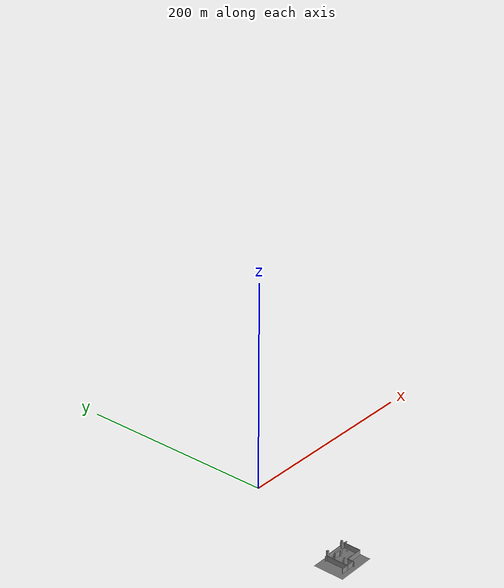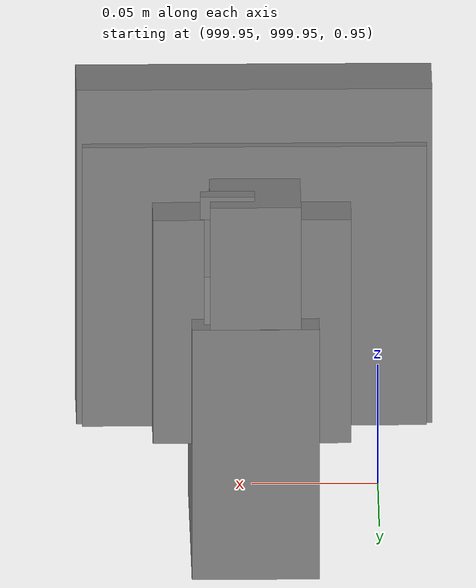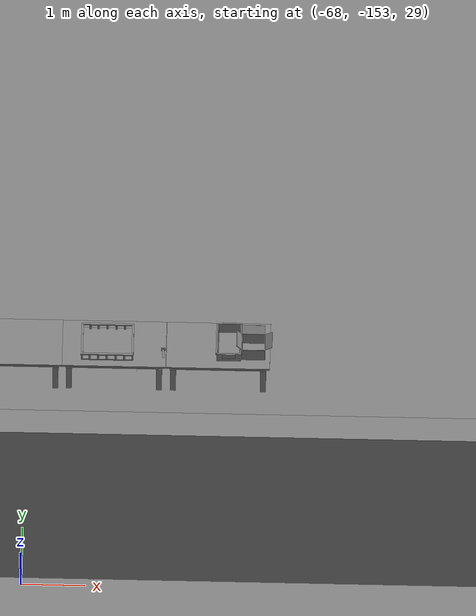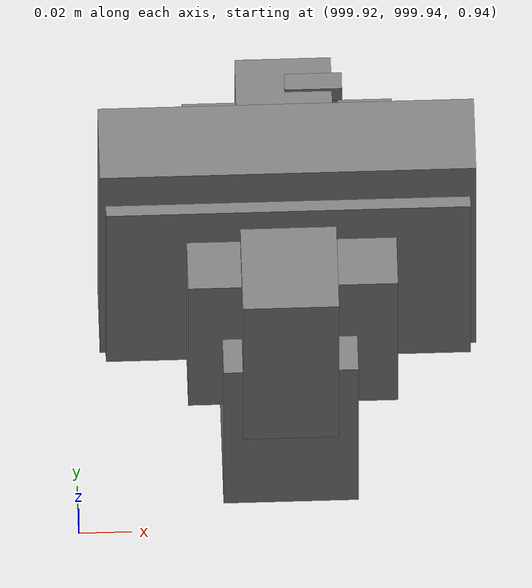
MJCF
<mujoco>
    <option gravity="0.000000000 0.000000000 -9.810000420" timestep="0.0049999999" integrator="implicitfast" density="1.225" viscosity="1.8000001e-05" noslip_iterations="10" iterations="100" sdf_iterations="50">
        <flag multiccd="disable"/>
    </option>
    <size memory="1000M"/>
    <compiler coordinate="local"/>
    <worldbody>
        <light cutoff="30" pos="0 1 1" dir="0 -1 -2"/>
        <light cutoff="30" pos="0 -1 1" dir="0 1 -2"/>
        <body pos="-64.866622925 -149.383972168 30.183746338" euler="89.999984741 89.999946594 0.000000000" name="openloong_gripper_2f85_fix_base_usda_bluebox_01">
            <geom contype="1" conaffinity="1" density="1000" type="box" material="" rgba="0.500000000 0.500000000 0.500000000 1.000000000" solimp="0.899999976 0.949999988 0.001000000" friction="1.000000000 0.005000000 0.000100000" solref="0.020000000 1.000000000" margin="0" condim="3" group="0" pos="0.276580811 0.187225342 0.000068665" quat="0.707106948 0.000077471 0.707106352 0.000077486" size="0.100000001 0.057999998 0.010000000" name="openloong_gripper_2f85_fix_base_usda_geom_DD7D0EDD_A9D2_42B6_912B_DB34F484BCF9"/>
            <geom contype="1" conaffinity="1" density="1000" type="box" material="" rgba="0.500000000 0.500000000 0.500000000 1.000000000" solimp="0.899999976 0.949999988 0.001000000" friction="1.000000000 0.005000000 0.000100000" solref="0.020000000 1.000000000" margin="0" condim="3" group="0" pos="0.000000000 0.002883911 0.000000000" quat="0.999999881 0.000000000 0.000000000 0.000000000" size="0.254000008 0.003000000 0.172000006" name="openloong_gripper_2f85_fix_base_usda_geom_DE095836_00DB_4584_B69C_FC4578FD5911"/>
            <geom contype="1" conaffinity="1" density="1000" type="box" material="" rgba="0.500000000 0.500000000 0.500000000 1.000000000" solimp="0.899999976 0.949999988 0.001000000" friction="1.000000000 0.005000000 0.000100000" solref="0.020000000 1.000000000" margin="0" condim="3" group="0" pos="0.000000000 0.124874115 0.173484802" quat="0.999796331 0.020176515 -0.000000015 0.000000030" size="0.259999990 0.119999997 0.007000000" name="openloong_gripper_2f85_fix_base_usda_geom_8AAF1BAE_8EBB_47B6_B86A_244751B57C28"/>
            <geom contype="1" conaffinity="1" density="1000" type="box" material="" rgba="0.500000000 0.500000000 0.500000000 1.000000000" solimp="0.899999976 0.949999988 0.001000000" friction="1.000000000 0.005000000 0.000100000" solref="0.020000000 1.000000000" margin="0" condim="3" group="0" pos="0.000000000 0.124874115 -0.173469543" quat="0.999796331 -0.020176545 -0.000000015 0.000000000" size="0.259999990 0.119999997 0.007000000" name="openloong_gripper_2f85_fix_base_usda_geom_B9D90B4A_797E_4F5A_8966_2B25CCA5F215"/>
            <geom contype="1" conaffinity="1" density="1000" type="box" material="" rgba="0.500000000 0.500000000 0.500000000 1.000000000" solimp="0.899999976 0.949999988 0.001000000" friction="1.000000000 0.005000000 0.000100000" solref="0.020000000 1.000000000" margin="0" condim="3" group="0" pos="0.000000000 0.214008331 0.188980103" quat="0.999912977 0.013176724 0.000000015 0.000000000" size="0.259999990 0.029999999 0.012500000" name="openloong_gripper_2f85_fix_base_usda_geom_42ECD5E8_78D0_4113_8EE5_31BC0B5E92BF"/>
            <geom contype="1" conaffinity="1" density="1000" type="box" material="" rgba="0.500000000 0.500000000 0.500000000 1.000000000" solimp="0.899999976 0.949999988 0.001000000" friction="1.000000000 0.005000000 0.000100000" solref="0.020000000 1.000000000" margin="0" condim="3" group="0" pos="-0.258361816 0.125289917 0.001876831" quat="0.702796936 -0.020792112 0.710783124 0.020769298" size="0.189999998 0.119999997 0.009000000" name="openloong_gripper_2f85_fix_base_usda_geom_2424CE87_7C8E_49F9_9189_158D2D303F31"/>
            <geom contype="1" conaffinity="1" density="1000" type="box" material="" rgba="0.500000000 0.500000000 0.500000000 1.000000000" solimp="0.899999976 0.949999988 0.001000000" friction="1.000000000 0.005000000 0.000100000" solref="0.020000000 1.000000000" margin="0" condim="3" group="0" pos="0.000000000 0.214008331 -0.188980103" quat="0.999912977 -0.013176769 0.000000030 0.000000015" size="0.259999990 0.029999999 0.012500000" name="openloong_gripper_2f85_fix_base_usda_geom_F119A939_8E0B_44A3_A829_F8C2AA0539F7"/>
            <geom contype="1" conaffinity="1" density="1000" type="box" material="" rgba="0.500000000 0.500000000 0.500000000 1.000000000" solimp="0.899999976 0.949999988 0.001000000" friction="1.000000000 0.005000000 0.000100000" solref="0.020000000 1.000000000" margin="0" condim="3" group="0" pos="-0.276611328 0.187225342 0.000068665" quat="0.707106650 0.000077441 0.707106709 0.000077456" size="0.100000001 0.057999998 0.010000000" name="openloong_gripper_2f85_fix_base_usda_geom_A08C31D6_9C8D_42FA_93AC_02C4A7570EDD"/>
            <geom contype="1" conaffinity="1" density="1000" type="box" material="" rgba="0.500000000 0.500000000 0.500000000 1.000000000" solimp="0.899999976 0.949999988 0.001000000" friction="1.000000000 0.005000000 0.000100000" solref="0.020000000 1.000000000" margin="0" condim="3" group="0" pos="0.258331299 0.125289917 0.001876831" quat="0.702851415 0.018856421 0.710823774 -0.019329369" size="0.189999998 0.119999997 0.009000000" name="openloong_gripper_2f85_fix_base_usda_geom_9532EC31_3AC6_433F_9BE3_6F1991B4C5A4"/>
            <freejoint name="openloong_gripper_2f85_fix_base_usda_bluebox_01_joint"/>
            <site size="0.005000000 0.005000000 0.005000000" rgba="0.500000000 0.500000000 0.500000000 1.000000000" pos="0.000000000 0.000000000 0.000000000" quat="0.999961913 0.008726534 0.000000000 0.000000000" group="0" type="sphere" name="openloong_gripper_2f85_fix_base_usda_bluebox_01site"/>
        </body>
        <body pos="-64.496299744 -149.491867065 30.235729218" euler="0.000000000 0.000000000 89.999946594" name="openloong_gripper_2f85_fix_base_usda_cardboardbox_01">
            <geom contype="1" conaffinity="1" density="1000" type="box" material="" rgba="0.500000000 0.500000000 0.500000000 1.000000000" solimp="0.899999976 0.949999988 0.001000000" friction="1.000000000 0.005000000 0.000100000" solref="0.020000000 1.000000000" margin="0" condim="3" group="0" pos="-0.003166199 -0.004086494 0.005052090" quat="1.000000000 0.000000000 0.000000000 0.000000000" size="0.142499998 0.177500010 0.005000000" name="openloong_gripper_2f85_fix_base_usda_geom_EA7D0CE5_D811_44B8_B383_49D499024796"/>
            <geom contype="1" conaffinity="1" density="1000" type="box" material="" rgba="0.500000000 0.500000000 0.500000000 1.000000000" solimp="0.899999976 0.949999988 0.001000000" friction="1.000000000 0.005000000 0.000100000" solref="0.020000000 1.000000000" margin="0" condim="3" group="0" pos="-0.003166199 0.170316696 0.150570869" quat="1.000000000 0.000000000 0.000000000 0.000000000" size="0.142499998 0.005000000 0.149999991" name="openloong_gripper_2f85_fix_base_usda_geom_B692F960_B586_46B6_B499_79E05F4CABA7"/>
            <geom contype="1" conaffinity="1" density="1000" type="box" material="" rgba="0.500000000 0.500000000 0.500000000 1.000000000" solimp="0.899999976 0.949999988 0.001000000" friction="1.000000000 0.005000000 0.000100000" solref="0.020000000 1.000000000" margin="0" condim="3" group="0" pos="-0.147399902 -0.005307198 0.150570869" quat="1.000000000 0.000000000 0.000000000 0.000000000" size="0.005000000 0.177500010 0.149999991" name="openloong_gripper_2f85_fix_base_usda_geom_1B52B4C3_CAA0_47F3_9746_E3A79750114C"/>
            <geom contype="1" conaffinity="1" density="1000" type="box" material="" rgba="0.500000000 0.500000000 0.500000000 1.000000000" solimp="0.899999976 0.949999988 0.001000000" friction="1.000000000 0.005000000 0.000100000" solref="0.020000000 1.000000000" margin="0" condim="3" group="0" pos="0.140275955 -0.005307198 0.150570869" quat="1.000000000 0.000000000 0.000000000 0.000000000" size="0.005000000 0.177500010 0.149999991" name="openloong_gripper_2f85_fix_base_usda_geom_23FA2617_E3AF_4303_BACF_B6F2A6555116"/>
            <geom contype="1" conaffinity="1" density="1000" type="box" material="" rgba="0.500000000 0.500000000 0.500000000 1.000000000" solimp="0.899999976 0.949999988 0.001000000" friction="1.000000000 0.005000000 0.000100000" solref="0.020000000 1.000000000" margin="0" condim="3" group="0" pos="-0.003166199 -0.181550980 0.150570869" quat="1.000000000 0.000000000 0.000000000 0.000000000" size="0.142499998 0.005000000 0.149999991" name="openloong_gripper_2f85_fix_base_usda_geom_8C09B1D2_3BAC_4118_B058_F8FEFF3F6097"/>
            <freejoint name="openloong_gripper_2f85_fix_base_usda_cardboardbox_01_joint"/>
            <site size="0.005000000 0.005000000 0.005000000" rgba="0.500000000 0.500000000 0.500000000 1.000000000" pos="0.000000000 0.000000000 0.000000000" quat="0.999961913 0.008726535 0.000000000 0.000000000" group="0" type="sphere" name="openloong_gripper_2f85_fix_base_usda_site_978720E1_58C6_4B17_B23E_4E1E0A9F4788"/>
            <body pos="0.139160156 -0.004048347 0.301930904" euler="-179.999954224 49.383502960 179.999954224" name="openloong_gripper_2f85_fix_base_usda_A1_006">
                <geom contype="1" conaffinity="1" density="1000" type="box" material="" rgba="0.500000000 0.500000000 0.500000000 1.000000000" solimp="0.899999976 0.949999988 0.001000000" friction="1.000000000 0.005000000 0.000100000" solref="0.020000000 1.000000000" margin="0" condim="3" group="0" pos="-0.071587563 0.000009537 0.001745224" quat="0.999999881 0.000000000 0.000000000 0.000000000" size="0.071249999 0.179999992 0.002500000" name="openloong_gripper_2f85_fix_base_usda_geom_B1EF190E_0E83_4075_BEF4_156406879C1F"/>
                <joint armature="0" stiffness="0.07" damping="0.0099999998" axis="0.000000 1.000000 0.000000" type="hinge" name="openloong_gripper_2f85_fix_base_usda_A1_006"/>
            </body>
            <body pos="-0.145902634 -0.004086494 0.301938057" euler="-180.000000000 -60.000011444 -180.000000000" name="openloong_gripper_2f85_fix_base_usda_A2_006">
                <geom contype="1" conaffinity="1" density="1000" type="box" material="" rgba="0.500000000 0.500000000 0.500000000 1.000000000" solimp="0.899999976 0.949999988 0.001000000" friction="1.000000000 0.005000000 0.000100000" solref="0.020000000 1.000000000" margin="0" condim="3" group="0" pos="0.071268082 0.000009537 0.002717972" quat="0.000002921 0.000000000 -0.000000030 0.999999881" size="0.071249999 0.179999992 0.002500000" name="openloong_gripper_2f85_fix_base_usda_geom_DA016CED_6D1F_49C1_918C_80D38E823675"/>
                <joint armature="0" stiffness="0.07" damping="0.0099999998" axis="0.000000 1.000000 0.000000" type="hinge" name="openloong_gripper_2f85_fix_base_usda_A2_006"/>
            </body>
            <body pos="-0.003385544 0.175991058 0.301930904" euler="-125.858116150 -0.000004561 0.000002331" name="openloong_gripper_2f85_fix_base_usda_B2_006">
                <geom contype="1" conaffinity="1" density="1000" type="box" material="" rgba="0.500000000 0.500000000 0.500000000 1.000000000" solimp="0.899999976 0.949999988 0.001000000" friction="1.000000000 0.005000000 0.000100000" solref="0.020000000 1.000000000" margin="0" condim="3" group="0" pos="0.000009537 -0.070939064 -0.002470016" quat="0.999614120 0.027776197 -0.000000015 0.000000030" size="0.137500003 0.064999998 0.005000000" name="openloong_gripper_2f85_fix_base_usda_geom_2F692C33_6565_455F_9A6C_A75AE49756DC"/>
                <joint armature="0" stiffness="0.07" damping="0.0099999998" axis="1.000000 0.000000 0.000000" type="hinge" name="openloong_gripper_2f85_fix_base_usda_B2_006"/>
            </body>
            <body pos="-0.003385544 -0.184140205 0.301938057" euler="147.805557251 0.000000000 0.000000000" name="openloong_gripper_2f85_fix_base_usda_B1_006">
                <geom contype="1" conaffinity="1" density="1000" type="box" material="" rgba="0.500000000 0.500000000 0.500000000 1.000000000" solimp="0.899999976 0.949999988 0.001000000" friction="1.000000000 0.005000000 0.000100000" solref="0.020000000 1.000000000" margin="0" condim="3" group="0" pos="-0.000028610 0.070202351 -0.002703667" quat="0.999614179 -0.027776167 0.000000000 0.000000000" size="0.137500003 0.064999998 0.005000000" name="openloong_gripper_2f85_fix_base_usda_geom_76F53564_C312_498D_BE1E_5199CAFCFF94"/>
                <joint armature="0" stiffness="0.07" damping="0.0099999998" axis="1.000000 0.000000 0.000000" type="hinge" name="openloong_gripper_2f85_fix_base_usda_B1_006"/>
            </body>
        </body>
        <body pos="-65.882858276 -149.481979370 30.229999542" euler="-64.487716675 0.000000000 0.000000000" name="openloong_gripper_2f85_fix_base_usda_Barcode">
            <geom contype="1" conaffinity="1" density="1000" type="box" material="" rgba="0.500000000 0.500000000 0.500000000 1.000000000" solimp="0.899999976 0.949999988 0.001000000" friction="1.000000000 0.005000000 0.000100000" solref="0.020000000 1.000000000" margin="0" condim="3" group="0" pos="0.000000000 0.013038635 0.001419067" quat="0.000000000 0.000000000 0.000000000 1.000000119" size="0.034000002 0.010000000 0.017999999" name="openloong_gripper_2f85_fix_base_usda_geom_6B233EAD_9674_4A44_A772_58B74E70EC38"/>
            <geom contype="1" conaffinity="1" density="1000" type="box" material="" rgba="0.500000000 0.500000000 0.500000000 1.000000000" solimp="0.899999976 0.949999988 0.001000000" friction="1.000000000 0.005000000 0.000100000" solref="0.020000000 1.000000000" margin="0" condim="3" group="0" pos="0.000000000 -0.035301208 -0.007095337" quat="0.000000000 0.000000000 -0.043619365 0.999048233" size="0.028999999 0.010000000 0.020000000" name="openloong_gripper_2f85_fix_base_usda_geom_F96BE5B0_0E47_4168_9AF5_30B0D95CD706"/>
            <geom contype="1" conaffinity="1" density="1000" type="box" material="" rgba="0.500000000 0.500000000 0.500000000 1.000000000" solimp="0.899999976 0.949999988 0.001000000" friction="1.000000000 0.005000000 0.000100000" solref="0.020000000 1.000000000" margin="0" condim="3" group="0" pos="0.000000000 -0.043411255 -0.011749268" quat="0.922262907 0.386563420 0.000000000 0.000000000" size="0.026000001 0.010000000 0.020000000" name="openloong_gripper_2f85_fix_base_usda_geom_ADCBB626_1140_457B_BC57_E7CC367FF622"/>
            <geom contype="1" conaffinity="1" density="1000" type="box" material="" rgba="0.500000000 0.500000000 0.500000000 1.000000000" solimp="0.899999976 0.949999988 0.001000000" friction="1.000000000 0.005000000 0.000100000" solref="0.020000000 1.000000000" margin="0" condim="3" group="0" pos="0.000000000 -0.016967773 -0.031860352" quat="0.000000000 0.000000000 0.000000000 1.000000119" size="0.008000000 0.010000000 0.013000000" name="openloong_gripper_2f85_fix_base_usda_geom_BC6B1129_7D66_4904_9127_2442670714A9"/>
            <geom contype="1" conaffinity="1" density="1000" type="box" material="" rgba="0.500000000 0.500000000 0.500000000 1.000000000" solimp="0.899999976 0.949999988 0.001000000" friction="1.000000000 0.005000000 0.000100000" solref="0.020000000 1.000000000" margin="0" condim="3" group="0" pos="0.000000000 -0.001869202 0.000312805" quat="0.953716993 0.300705761 0.000000000 0.000000000" size="0.032000002 0.010000000 0.018999999" name="openloong_gripper_2f85_fix_base_usda_geom_11ADD26C_00CC_400A_AF52_3E85F09B02BF"/>
            <geom contype="1" conaffinity="1" density="1000" type="box" material="" rgba="0.500000000 0.500000000 0.500000000 1.000000000" solimp="0.899999976 0.949999988 0.001000000" friction="1.000000000 0.005000000 0.000100000" solref="0.020000000 1.000000000" margin="0" condim="3" group="0" pos="0.000000000 -0.019531250 -0.003173828" quat="0.953716993 0.300705761 0.000000000 0.000000000" size="0.030999999 0.010000000 0.020000000" name="openloong_gripper_2f85_fix_base_usda_geom_A0105CF6_2FDC_4B58_8D0F_6C20BEB92A4E"/>
            <geom contype="1" conaffinity="1" density="1000" type="box" material="" rgba="0.500000000 0.500000000 0.500000000 1.000000000" solimp="0.899999976 0.949999988 0.001000000" friction="1.000000000 0.005000000 0.000100000" solref="0.020000000 1.000000000" margin="0" condim="3" group="0" pos="0.000000000 -0.035301208 -0.007095337" quat="0.953716993 0.300705761 0.000000000 0.000000000" size="0.028999999 0.010000000 0.020000000" name="openloong_gripper_2f85_fix_base_usda_geom_4AC125B3_358D_49AC_AB08_B57F23C4A54F"/>
            <geom contype="1" conaffinity="1" density="1000" type="box" material="" rgba="0.500000000 0.500000000 0.500000000 1.000000000" solimp="0.899999976 0.949999988 0.001000000" friction="1.000000000 0.005000000 0.000100000" solref="0.020000000 1.000000000" margin="0" condim="3" group="0" pos="0.000000000 -0.042617798 -0.071121216" quat="0.000000000 0.000000000 0.000000000 1.000000119" size="0.013000000 0.021000000 0.059999999" name="openloong_gripper_2f85_fix_base_usda_geom_EAC48BAF_7854_400D_9B42_19C16D426DBE"/>
            <freejoint name="openloong_gripper_2f85_fix_base_usda_Barcode_joint"/>
            <site size="0.005000000 0.005000000 0.005000000" rgba="0.500000000 0.500000000 0.500000000 1.000000000" pos="0.000000000 0.000000000 0.000000000" quat="1.000000000 0.000000000 0.000000000 0.000000000" group="0" type="sphere" name="openloong_gripper_2f85_fix_base_usda_Barcode_site"/>
        </body>
        <body pos="-66.745018005 -149.392349243 30.184000015" euler="0.000000000 0.000000000 89.999946594" name="[22330444584764]_Basket_01">
            <geom contype="1" conaffinity="1" density="1000" type="box" material="" rgba="0.500000000 0.500000000 0.500000000 1.000000000" solimp="0.899999976 0.949999988 0.001000000" friction="1.000000000 0.005000000 0.000100000" solref="0.020000000 1.000000000" margin="0" condim="3" group="0" pos="-0.052425385 0.389207840 0.089787483" quat="0.707107008 0.000000000 0.000000000 0.707106411" size="0.014249999 0.014249999 0.059999999" name="[22330444584764]_geom_44504030_CBFC_4C07_8609_FB79262A4021"/>
            <geom contype="1" conaffinity="1" density="1000" type="box" material="" rgba="0.500000000 0.500000000 0.500000000 1.000000000" solimp="0.899999976 0.949999988 0.001000000" friction="1.000000000 0.005000000 0.000100000" solref="0.020000000 1.000000000" margin="0" condim="3" group="0" pos="0.264015198 -0.133043289 0.089787483" quat="0.707107008 0.000000000 0.000000000 0.707106411" size="0.014249999 0.014249999 0.059999999" name="[22330444584764]_geom_4E8FF8C9_1EBD_4450_87ED_1E60FDEB1563"/>
            <geom contype="1" conaffinity="1" density="1000" type="box" material="" rgba="0.500000000 0.500000000 0.500000000 1.000000000" solimp="0.899999976 0.949999988 0.001000000" friction="1.000000000 0.005000000 0.000100000" solref="0.020000000 1.000000000" margin="0" condim="3" group="0" pos="-0.264015198 -0.265548706 0.089793205" quat="0.707107008 0.000000000 0.000000000 0.707106411" size="0.014249999 0.014249999 0.059999999" name="[22330444584764]_geom_582A2CE1_7CA9_4A3C_A4AD_92F5D51F4BAE"/>
            <geom contype="1" conaffinity="1" density="1000" type="box" material="" rgba="0.500000000 0.500000000 0.500000000 1.000000000" solimp="0.899999976 0.949999988 0.001000000" friction="1.000000000 0.005000000 0.000100000" solref="0.020000000 1.000000000" margin="0" condim="3" group="0" pos="-0.160263062 -0.389322281 0.089793205" quat="0.707107008 0.000000000 0.000000000 0.707106411" size="0.014249999 0.014249999 0.059999999" name="[22330444584764]_geom_1135AA43_7B82_4E43_8C0F_B5DDD9A59AAD"/>
            <geom contype="1" conaffinity="1" density="1000" type="box" material="" rgba="0.500000000 0.500000000 0.500000000 1.000000000" solimp="0.899999976 0.949999988 0.001000000" friction="1.000000000 0.005000000 0.000100000" solref="0.020000000 1.000000000" margin="0" condim="3" group="0" pos="0.162265778 -0.389322281 0.089787483" quat="0.707107008 0.000000000 0.000000000 0.707106411" size="0.014249999 0.014249999 0.059999999" name="[22330444584764]_geom_CFA55BC6_BB71_4263_BF2B_127FF0AB16F6"/>
            <geom contype="1" conaffinity="1" density="1000" type="box" material="" rgba="0.500000000 0.500000000 0.500000000 1.000000000" solimp="0.899999976 0.949999988 0.001000000" friction="1.000000000 0.005000000 0.000100000" solref="0.020000000 1.000000000" margin="0" condim="3" group="0" pos="0.264015198 0.389207840 0.089787483" quat="0.707107008 0.000000000 0.000000000 0.707106411" size="0.014249999 0.014249999 0.059999999" name="[22330444584764]_geom_41C5BDEF_D43D_43EE_8684_92057C78DDE1"/>
            <geom contype="1" conaffinity="1" density="1000" type="box" material="" rgba="0.500000000 0.500000000 0.500000000 1.000000000" solimp="0.899999976 0.949999988 0.001000000" friction="1.000000000 0.005000000 0.000100000" solref="0.020000000 1.000000000" margin="0" condim="3" group="0" pos="-0.264015198 -0.133043289 0.089793205" quat="0.707107008 0.000000000 0.000000000 0.707106411" size="0.014249999 0.014249999 0.059999999" name="[22330444584764]_geom_B857357C_28A8_451B_8ECF_C8C5431DC647"/>
            <geom contype="1" conaffinity="1" density="1000" type="box" material="" rgba="0.500000000 0.500000000 0.500000000 1.000000000" solimp="0.899999976 0.949999988 0.001000000" friction="1.000000000 0.005000000 0.000100000" solref="0.020000000 1.000000000" margin="0" condim="3" group="0" pos="-0.264026642 0.269256592 0.089793205" quat="0.707107008 0.000000000 0.000000000 0.707106411" size="0.014249999 0.014249999 0.059999999" name="[22330444584764]_geom_D82AAFD6_8406_4542_A504_A665D624D787"/>
            <geom contype="1" conaffinity="1" density="1000" type="box" material="" rgba="0.500000000 0.500000000 0.500000000 1.000000000" solimp="0.899999976 0.949999988 0.001000000" friction="1.000000000 0.005000000 0.000100000" solref="0.020000000 1.000000000" margin="0" condim="3" group="0" pos="0.054462433 0.389207840 0.089787483" quat="0.707107008 0.000000000 0.000000000 0.707106411" size="0.014249999 0.014249999 0.059999999" name="[22330444584764]_geom_F68E5BFA_681B_462E_B19D_99A5231325DA"/>
            <geom contype="1" conaffinity="1" density="1000" type="box" material="" rgba="0.500000000 0.500000000 0.500000000 1.000000000" solimp="0.899999976 0.949999988 0.001000000" friction="1.000000000 0.005000000 0.000100000" solref="0.020000000 1.000000000" margin="0" condim="3" group="0" pos="0.054462433 -0.389322281 0.089787483" quat="0.707107008 0.000000000 0.000000000 0.707106411" size="0.014249999 0.014249999 0.059999999" name="[22330444584764]_geom_D361B358_D607_4819_AAD2_92F968FE004A"/>
            <geom contype="1" conaffinity="1" density="1000" type="box" material="" rgba="0.500000000 0.500000000 0.500000000 1.000000000" solimp="0.899999976 0.949999988 0.001000000" friction="1.000000000 0.005000000 0.000100000" solref="0.020000000 1.000000000" margin="0" condim="3" group="0" pos="0.264015198 0.269256592 0.089793205" quat="0.707107008 0.000000000 0.000000000 0.707106411" size="0.014249999 0.014249999 0.059999999" name="[22330444584764]_geom_2BE59A5B_B2F9_42AB_8769_A5E1DFDB41A0"/>
            <geom contype="1" conaffinity="1" density="1000" type="box" material="" rgba="0.500000000 0.500000000 0.500000000 1.000000000" solimp="0.899999976 0.949999988 0.001000000" friction="1.000000000 0.005000000 0.000100000" solref="0.020000000 1.000000000" margin="0" condim="3" group="0" pos="0.264015198 -0.389322281 0.089787483" quat="0.707107008 0.000000000 0.000000000 0.707106411" size="0.014249999 0.014249999 0.059999999" name="[22330444584764]_geom_92421812_4E3E_4AF6_91D4_B2B5644AE7D6"/>
            <geom contype="1" conaffinity="1" density="1000" type="box" material="" rgba="0.500000000 0.500000000 0.500000000 1.000000000" solimp="0.899999976 0.949999988 0.001000000" friction="1.000000000 0.005000000 0.000100000" solref="0.020000000 1.000000000" margin="0" condim="3" group="0" pos="0.000000000 0.000000000 0.015998840" quat="0.707107008 0.000000000 0.000000000 0.707106411" size="0.403499991 0.279000014 0.015750000" name="[22330444584764]_geom_05FC1DE2_101C_4237_97BF_7A64B636976E"/>
            <geom contype="1" conaffinity="1" density="1000" type="box" material="" rgba="0.500000000 0.500000000 0.500000000 1.000000000" solimp="0.899999976 0.949999988 0.001000000" friction="1.000000000 0.005000000 0.000100000" solref="0.020000000 1.000000000" margin="0" condim="3" group="0" pos="0.000000000 -0.389476776 0.163619041" quat="0.707107008 0.000000000 0.000000000 0.707106411" size="0.015000000 0.277500004 0.015750000" name="[22330444584764]_geom_54C5B864_8119_466B_AD21_80839C4F7867"/>
            <geom contype="1" conaffinity="1" density="1000" type="box" material="" rgba="0.500000000 0.500000000 0.500000000 1.000000000" solimp="0.899999976 0.949999988 0.001000000" friction="1.000000000 0.005000000 0.000100000" solref="0.020000000 1.000000000" margin="0" condim="3" group="0" pos="0.162265778 0.389207840 0.089787483" quat="0.707107008 0.000000000 0.000000000 0.707106411" size="0.014249999 0.014249999 0.059999999" name="[22330444584764]_geom_20A16B79_D80F_467B_9C03_520F8A41A1D4"/>
            <geom contype="1" conaffinity="1" density="1000" type="box" material="" rgba="0.500000000 0.500000000 0.500000000 1.000000000" solimp="0.899999976 0.949999988 0.001000000" friction="1.000000000 0.005000000 0.000100000" solref="0.020000000 1.000000000" margin="0" condim="3" group="0" pos="0.000000000 0.389471054 0.163619041" quat="0.707107008 0.000000000 0.000000000 0.707106411" size="0.015000000 0.277500004 0.015750000" name="[22330444584764]_geom_81D2FD3C_5D9E_4FE6_BC9A_B3059777FE09"/>
            <geom contype="1" conaffinity="1" density="1000" type="box" material="" rgba="0.500000000 0.500000000 0.500000000 1.000000000" solimp="0.899999976 0.949999988 0.001000000" friction="1.000000000 0.005000000 0.000100000" solref="0.020000000 1.000000000" margin="0" condim="3" group="0" pos="-0.263511658 0.000000000 0.163619041" quat="0.707107008 0.000000000 0.000000000 0.707106411" size="0.403499991 0.015000000 0.015750000" name="[22330444584764]_geom_31249405_0904_4D8D_81F5_BD9C79954FB4"/>
            <geom contype="1" conaffinity="1" density="1000" type="box" material="" rgba="0.500000000 0.500000000 0.500000000 1.000000000" solimp="0.899999976 0.949999988 0.001000000" friction="1.000000000 0.005000000 0.000100000" solref="0.020000000 1.000000000" margin="0" condim="3" group="0" pos="-0.264015198 0.141334534 0.089793205" quat="0.707107008 0.000000000 0.000000000 0.707106411" size="0.014249999 0.014249999 0.059999999" name="[22330444584764]_geom_4FF38FA7_FC7D_4588_8EEB_A414F8FFF4B7"/>
            <geom contype="1" conaffinity="1" density="1000" type="box" material="" rgba="0.500000000 0.500000000 0.500000000 1.000000000" solimp="0.899999976 0.949999988 0.001000000" friction="1.000000000 0.005000000 0.000100000" solref="0.020000000 1.000000000" margin="0" condim="3" group="0" pos="0.264015198 -0.265548706 0.089787483" quat="0.707107008 0.000000000 0.000000000 0.707106411" size="0.014249999 0.014249999 0.059999999" name="[22330444584764]_geom_09FB64DD_D05B_4C0A_96DE_A820D50C8BD3"/>
            <geom contype="1" conaffinity="1" density="1000" type="box" material="" rgba="0.500000000 0.500000000 0.500000000 1.000000000" solimp="0.899999976 0.949999988 0.001000000" friction="1.000000000 0.005000000 0.000100000" solref="0.020000000 1.000000000" margin="0" condim="3" group="0" pos="-0.160263062 0.389207840 0.089787483" quat="0.707107008 0.000000000 0.000000000 0.707106411" size="0.014249999 0.014249999 0.059999999" name="[22330444584764]_geom_41395310_7E17_400C_B8BF_E91AF7DB78AD"/>
            <geom contype="1" conaffinity="1" density="1000" type="box" material="" rgba="0.500000000 0.500000000 0.500000000 1.000000000" solimp="0.899999976 0.949999988 0.001000000" friction="1.000000000 0.005000000 0.000100000" solref="0.020000000 1.000000000" margin="0" condim="3" group="0" pos="-0.052425385 -0.389322281 0.089787483" quat="0.707107008 0.000000000 0.000000000 0.707106411" size="0.014249999 0.014249999 0.059999999" name="[22330444584764]_geom_72D3B278_AD6B_492E_9762_A1E666515B30"/>
            <geom contype="1" conaffinity="1" density="1000" type="box" material="" rgba="0.500000000 0.500000000 0.500000000 1.000000000" solimp="0.899999976 0.949999988 0.001000000" friction="1.000000000 0.005000000 0.000100000" solref="0.020000000 1.000000000" margin="0" condim="3" group="0" pos="-0.264026642 -0.389322281 0.089793205" quat="0.707107008 0.000000000 0.000000000 0.707106411" size="0.014249999 0.014249999 0.059999999" name="[22330444584764]_geom_2376F65F_BD64_47C8_B46B_A66E7212B5D1"/>
            <geom contype="1" conaffinity="1" density="1000" type="box" material="" rgba="0.500000000 0.500000000 0.500000000 1.000000000" solimp="0.899999976 0.949999988 0.001000000" friction="1.000000000 0.005000000 0.000100000" solref="0.020000000 1.000000000" margin="0" condim="3" group="0" pos="0.264015198 0.141334534 0.089787483" quat="0.707107008 0.000000000 0.000000000 0.707106411" size="0.014249999 0.014249999 0.059999999" name="[22330444584764]_geom_3D8D0BC8_2496_47FD_BF8B_FFF0394FB122"/>
            <geom contype="1" conaffinity="1" density="1000" type="box" material="" rgba="0.500000000 0.500000000 0.500000000 1.000000000" solimp="0.899999976 0.949999988 0.001000000" friction="1.000000000 0.005000000 0.000100000" solref="0.020000000 1.000000000" margin="0" condim="3" group="0" pos="-0.264015198 0.389207840 0.089793205" quat="0.707107008 0.000000000 0.000000000 0.707106411" size="0.014249999 0.014249999 0.059999999" name="[22330444584764]_geom_B5B23E08_39BC_4FB8_835F_BA1252B3218E"/>
            <geom contype="1" conaffinity="1" density="1000" type="box" material="" rgba="0.500000000 0.500000000 0.500000000 1.000000000" solimp="0.899999976 0.949999988 0.001000000" friction="1.000000000 0.005000000 0.000100000" solref="0.020000000 1.000000000" margin="0" condim="3" group="0" pos="0.264015198 0.004480362 0.089787483" quat="0.707107008 0.000000000 0.000000000 0.707106411" size="0.014249999 0.014249999 0.059999999" name="[22330444584764]_geom_CA8E166F_9F41_4966_AC90_2F1FF2AD2F70"/>
            <geom contype="1" conaffinity="1" density="1000" type="box" material="" rgba="0.500000000 0.500000000 0.500000000 1.000000000" solimp="0.899999976 0.949999988 0.001000000" friction="1.000000000 0.005000000 0.000100000" solref="0.020000000 1.000000000" margin="0" condim="3" group="0" pos="0.263694763 -0.000011444 0.163619041" quat="0.707107008 0.000000000 0.000000000 0.707106411" size="0.403499991 0.015000000 0.015750000" name="[22330444584764]_geom_A42A72CE_3EB7_4087_9E59_2A7EFEAA0B02"/>
            <geom contype="1" conaffinity="1" density="1000" type="box" material="" rgba="0.500000000 0.500000000 0.500000000 1.000000000" solimp="0.899999976 0.949999988 0.001000000" friction="1.000000000 0.005000000 0.000100000" solref="0.020000000 1.000000000" margin="0" condim="3" group="0" pos="-0.264015198 0.004480362 0.089793205" quat="0.707107008 0.000000000 0.000000000 0.707106411" size="0.014249999 0.014249999 0.059999999" name="[22330444584764]_geom_285CB8F1_E7AB_428B_BB56_8706DFDB07FC"/>
            <freejoint name="[22330444584764]_joint_7C5E10E6_022C_4A62_9848_AA3B501548A4"/>
        </body>
        <body pos="0.000000000 0.000000000 0.000000000" euler="0.000000000 0.000000000 0.000000000" name="Static Objects_Static Objects">
            <geom contype="1" conaffinity="1" density="1000" type="box" material="" rgba="0.500000000 0.500000000 0.500000000 1.000000000" solimp="0.899999976 0.949999988 0.001000000" friction="1.000000000 0.005000000 0.000100000" solref="0.020000000 1.000000000" margin="0" condim="3" group="0" pos="-67.544113159 -149.365814209 29.727830887" quat="0.500000417 0.499999970 0.499999553 0.499999970" size="0.381000012 0.319999993 0.041000001" name="Static Objects_geom_FA6AFC60_00D1_41A3_9AA2_96C66CDD294B"/>
            <geom contype="1" conaffinity="1" density="1000" type="box" material="" rgba="0.500000000 0.500000000 0.500000000 1.000000000" solimp="0.899999976 0.949999988 0.001000000" friction="1.000000000 0.005000000 0.000100000" solref="0.020000000 1.000000000" margin="0" condim="3" group="0" pos="-68.239501953 -149.365814209 30.086868286" quat="0.500000417 0.499999970 0.499999553 0.499999970" size="0.370999992 0.039500002 0.745000005" name="Static Objects_geom_CF112FED_052B_4635_96ED_AB26C6430779"/>
            <geom contype="1" conaffinity="1" density="1000" type="box" material="" rgba="0.500000000 0.500000000 0.500000000 1.000000000" solimp="0.899999976 0.949999988 0.001000000" friction="1.000000000 0.005000000 0.000100000" solref="0.020000000 1.000000000" margin="0" condim="3" group="0" pos="-68.239501953 -149.365814209 30.147235870" quat="0.500000417 0.499999970 0.499999553 0.499999970" size="0.400000006 0.022000000 0.800000012" name="Static Objects_geom_11BB48C6_107B_4813_B0FD_A95A72718FB6"/>
            <geom contype="1" conaffinity="1" density="1000" type="box" material="" rgba="0.500000000 0.500000000 0.500000000 1.000000000" solimp="0.899999976 0.949999988 0.001000000" friction="1.000000000 0.005000000 0.000100000" solref="0.020000000 1.000000000" margin="0" condim="3" group="0" pos="-68.934890747 -149.365814209 29.727830887" quat="0.500000417 0.499999970 0.499999553 0.499999970" size="0.381000012 0.319999993 0.041000001" name="Static Objects_geom_706D2CFE_2120_4566_93FD_1B72191A1C22"/>
            <geom contype="1" conaffinity="1" density="1000" type="box" material="" rgba="0.500000000 0.500000000 0.500000000 1.000000000" solimp="0.899999976 0.949999988 0.001000000" friction="1.000000000 0.005000000 0.000100000" solref="0.020000000 1.000000000" margin="0" condim="3" group="0" pos="-68.239501953 -149.365814209 29.561563492" quat="0.500000417 0.499999970 0.499999553 0.499999970" size="0.020000000 0.022000000 0.660000026" name="Static Objects_geom_0D481771_6917_449E_81DA_8C768D94B35C"/>
            <geom contype="1" conaffinity="1" density="1000" type="box" material="" rgba="0.500000000 0.500000000 0.500000000 1.000000000" solimp="0.899999976 0.949999988 0.001000000" friction="1.000000000 0.005000000 0.000100000" solref="0.020000000 1.000000000" margin="0" condim="3" group="0" pos="-65.945671082 -149.365814209 29.727830887" quat="0.500000417 0.499999970 0.499999553 0.499999970" size="0.381000012 0.319999993 0.041000001" name="Static Objects_geom_585D3EB6_B207_4A69_A1E7_16ACCE75547A"/>
            <geom contype="1" conaffinity="1" density="1000" type="box" material="" rgba="0.500000000 0.500000000 0.500000000 1.000000000" solimp="0.899999976 0.949999988 0.001000000" friction="1.000000000 0.005000000 0.000100000" solref="0.020000000 1.000000000" margin="0" condim="3" group="0" pos="-66.641059875 -149.365814209 30.086868286" quat="0.500000417 0.499999970 0.499999553 0.499999970" size="0.370999992 0.039500002 0.745000005" name="Static Objects_geom_B92419F8_9D58_4C72_947D_9189FF81D858"/>
            <geom contype="1" conaffinity="1" density="1000" type="box" material="" rgba="0.500000000 0.500000000 0.500000000 1.000000000" solimp="0.899999976 0.949999988 0.001000000" friction="1.000000000 0.005000000 0.000100000" solref="0.020000000 1.000000000" margin="0" condim="3" group="0" pos="-66.641059875 -149.365814209 30.147235870" quat="0.500000417 0.499999970 0.499999553 0.499999970" size="0.400000006 0.022000000 0.800000012" name="Static Objects_geom_8C61CC61_91B4_4FE4_A1CC_1C89AF82B48E"/>
            <geom contype="1" conaffinity="1" density="1000" type="box" material="" rgba="0.500000000 0.500000000 0.500000000 1.000000000" solimp="0.899999976 0.949999988 0.001000000" friction="1.000000000 0.005000000 0.000100000" solref="0.020000000 1.000000000" margin="0" condim="3" group="0" pos="-67.336448669 -149.365814209 29.727830887" quat="0.500000417 0.499999970 0.499999553 0.499999970" size="0.381000012 0.319999993 0.041000001" name="Static Objects_geom_4A6CAD84_5A9E_47A3_A7E4_D47E66001431"/>
            <geom contype="1" conaffinity="1" density="1000" type="box" material="" rgba="0.500000000 0.500000000 0.500000000 1.000000000" solimp="0.899999976 0.949999988 0.001000000" friction="1.000000000 0.005000000 0.000100000" solref="0.020000000 1.000000000" margin="0" condim="3" group="0" pos="-66.641059875 -149.365814209 29.561563492" quat="0.500000417 0.499999970 0.499999553 0.499999970" size="0.020000000 0.022000000 0.660000026" name="Static Objects_geom_0C85866F_891E_4847_AC2C_CA0EF9F126C2"/>
            <geom contype="1" conaffinity="1" density="1000" type="box" material="" rgba="0.500000000 0.500000000 0.500000000 1.000000000" solimp="0.899999976 0.949999988 0.001000000" friction="1.000000000 0.005000000 0.000100000" solref="0.020000000 1.000000000" margin="0" condim="3" group="0" pos="-64.338577271 -149.365814209 29.727830887" quat="0.500000417 0.499999970 0.499999553 0.499999970" size="0.381000012 0.319999993 0.041000001" name="Static Objects_geom_58650B07_083D_4DDD_8012_785882FED069"/>
            <geom contype="1" conaffinity="1" density="1000" type="box" material="" rgba="0.500000000 0.500000000 0.500000000 1.000000000" solimp="0.899999976 0.949999988 0.001000000" friction="1.000000000 0.005000000 0.000100000" solref="0.020000000 1.000000000" margin="0" condim="3" group="0" pos="-65.033966064 -149.365814209 30.086868286" quat="0.500000417 0.499999970 0.499999553 0.499999970" size="0.370999992 0.039500002 0.745000005" name="Static Objects_geom_78B8784A_CCBC_4210_A645_4DA38D39A1ED"/>
            <geom contype="1" conaffinity="1" density="1000" type="box" material="" rgba="0.500000000 0.500000000 0.500000000 1.000000000" solimp="0.899999976 0.949999988 0.001000000" friction="1.000000000 0.005000000 0.000100000" solref="0.020000000 1.000000000" margin="0" condim="3" group="0" pos="-65.033966064 -149.365814209 30.147235870" quat="0.500000417 0.499999970 0.499999553 0.499999970" size="0.400000006 0.022000000 0.800000012" name="Static Objects_geom_0661EAFC_8184_43E0_ADFD_532259016C87"/>
            <geom contype="1" conaffinity="1" density="1000" type="box" material="" rgba="0.500000000 0.500000000 0.500000000 1.000000000" solimp="0.899999976 0.949999988 0.001000000" friction="1.000000000 0.005000000 0.000100000" solref="0.020000000 1.000000000" margin="0" condim="3" group="0" pos="-65.729354858 -149.365814209 29.727830887" quat="0.500000417 0.499999970 0.499999553 0.499999970" size="0.381000012 0.319999993 0.041000001" name="Static Objects_geom_54034395_434B_4991_A427_109E72C1A288"/>
            <geom contype="1" conaffinity="1" density="1000" type="box" material="" rgba="0.500000000 0.500000000 0.500000000 1.000000000" solimp="0.899999976 0.949999988 0.001000000" friction="1.000000000 0.005000000 0.000100000" solref="0.020000000 1.000000000" margin="0" condim="3" group="0" pos="-65.033966064 -149.365814209 29.561563492" quat="0.500000417 0.499999970 0.499999553 0.499999970" size="0.020000000 0.022000000 0.660000026" name="Static Objects_geom_C386AAEF_F9BE_4C4E_9376_16A4642A5C73"/>
            <geom contype="1" conaffinity="1" density="1000" type="box" material="" rgba="0.500000000 0.500000000 0.500000000 1.000000000" solimp="0.899999976 0.949999988 0.001000000" friction="1.000000000 0.005000000 0.000100000" solref="0.020000000 1.000000000" margin="0" condim="3" group="0" pos="-61.754566193 -137.853729248 33.906845093" quat="0.707107067 0.000000000 0.000000000 0.707106471" size="0.759999990 0.759999990 4.500000000" name="Static Objects_geom_60A98A03_B8DE_4783_80F3_EA1AED6F24E9"/>
            <geom contype="1" conaffinity="1" density="1000" type="box" material="" rgba="0.500000000 0.500000000 0.500000000 1.000000000" solimp="0.899999976 0.949999988 0.001000000" friction="1.000000000 0.005000000 0.000100000" solref="0.020000000 1.000000000" margin="0" condim="3" group="0" pos="-57.511135101 -144.927108765 31.707921982" quat="1.000000000 0.000000000 0.000000000 0.000000000" size="0.200000003 8.000000000 2.299999952" name="Static Objects_geom_529CEC09_95A5_4626_9851_42453149D49C"/>
            <geom contype="1" conaffinity="1" density="1000" type="box" material="" rgba="0.500000000 0.500000000 0.500000000 1.000000000" solimp="0.899999976 0.949999988 0.001000000" friction="1.000000000 0.005000000 0.000100000" solref="0.020000000 1.000000000" margin="0" condim="3" group="0" pos="-80.517646790 -157.574050903 31.688196182" quat="0.707107067 0.000000000 0.000000000 0.707106471" size="0.600000024 0.600000024 2.299999952" name="Static Objects_geom_86D6C577_C037_4926_B22C_26E8F7479C51"/>
            <geom contype="1" conaffinity="1" density="1000" type="box" material="" rgba="0.500000000 0.500000000 0.500000000 1.000000000" solimp="0.899999976 0.949999988 0.001000000" friction="1.000000000 0.005000000 0.000100000" solref="0.020000000 1.000000000" margin="0" condim="3" group="0" pos="-80.711044312 -147.414932251 31.666158676" quat="1.000000000 0.000000000 0.000000000 0.000000000" size="0.200000003 10.000000000 2.299999952" name="Static Objects_geom_CD2DC803_7898_49DF_9636_547566A6D0E1"/>
            <geom contype="1" conaffinity="1" density="1000" type="box" material="" rgba="0.500000000 0.500000000 0.500000000 1.000000000" solimp="0.899999976 0.949999988 0.001000000" friction="1.000000000 0.005000000 0.000100000" solref="0.020000000 1.000000000" margin="0" condim="3" group="0" pos="-57.687217712 -137.434692383 31.688196182" quat="0.707107067 0.000000000 0.000000000 0.707106471" size="0.600000024 0.600000024 2.299999952" name="Static Objects_geom_73BCCCE8_7726_4E90_8D4A_54FD5F6B5138"/>
            <geom contype="1" conaffinity="1" density="1000" type="box" material="" rgba="0.500000000 0.500000000 0.500000000 1.000000000" solimp="0.899999976 0.949999988 0.001000000" friction="1.000000000 0.005000000 0.000100000" solref="0.020000000 1.000000000" margin="0" condim="3" group="0" pos="-69.537033081 -140.263229370 31.714921951" quat="0.707107067 0.000000000 0.000000000 0.707106471" size="0.759999990 4.500000000 2.299999952" name="Static Objects_geom_86C9F902_E0FE_4C13_BAF7_08BDA3779AE5"/>
            <geom contype="1" conaffinity="1" density="1000" type="box" material="" rgba="0.500000000 0.500000000 0.500000000 1.000000000" solimp="0.899999976 0.949999988 0.001000000" friction="1.000000000 0.005000000 0.000100000" solref="0.020000000 1.000000000" margin="0" condim="3" group="0" pos="-80.073638916 -137.853713989 33.906845093" quat="0.707107067 0.000000000 0.000000000 0.707106471" size="0.759999990 0.759999990 4.500000000" name="Static Objects_geom_541ECD50_B87A_4A05_9CC3_DCC71828B6D5"/>
            <geom contype="1" conaffinity="1" density="1000" type="box" material="" rgba="0.500000000 0.500000000 0.500000000 1.000000000" solimp="0.899999976 0.949999988 0.001000000" friction="1.000000000 0.005000000 0.000100000" solref="0.020000000 1.000000000" margin="0" condim="3" group="0" pos="-73.406707764 -155.734664917 31.707921982" quat="1.000000000 0.000000000 0.000000000 0.000000000" size="0.200000003 3.000000000 2.299999952" name="Static Objects_geom_D7F53E63_AA94_4E64_BE6C_74A15C17CE85"/>
            <geom contype="1" conaffinity="1" density="1000" type="box" material="" rgba="0.500000000 0.500000000 0.500000000 1.000000000" solimp="0.899999976 0.949999988 0.001000000" friction="1.000000000 0.005000000 0.000100000" solref="0.020000000 1.000000000" margin="0" condim="3" group="0" pos="-68.497543335 -137.448257446 31.707921982" quat="0.707107067 0.000000000 0.000000000 0.707106471" size="0.200000003 14.000000000 2.299999952" name="Static Objects_geom_9790E992_6D9A_42D8_85DF_C22F587C737F"/>
            <geom contype="1" conaffinity="1" density="1000" type="cylinder" material="" rgba="0.500000000 0.500000000 0.500000000 1.000000000" solimp="0.899999976 0.949999988 0.001000000" friction="1.000000000 0.005000000 0.000100000" solref="0.020000000 1.000000000" margin="0" condim="3" group="0" pos="-68.868522644 -142.134506226 31.711090088" quat="0.707107067 0.000000000 0.000000000 0.707106471" size="0.509999990 2.299999952 1.000000000" name="Static Objects_geom_EFE13A96_781C_4526_AAA2_224B020F72D8"/>
            <geom contype="1" conaffinity="1" density="1000" type="plane" material="" rgba="0.500000000 0.500000000 0.500000000 1.000000000" solimp="0.899999976 0.949999988 0.001000000" friction="1.000000000 0.005000000 0.000100000" solref="0.020000000 1.000000000" margin="0" condim="3" group="0" pos="-72.873703003 -147.131927490 29.409669876" quat="1.000000000 0.000000000 0.000000000 0.000000000" size="18.000000000 14.000000000 1.000000000" name="Static Objects_geom_1D4B2167_43F0_40C4_B190_B7A09599A7F3"/>
            <geom contype="1" conaffinity="1" density="1000" type="box" material="" rgba="0.500000000 0.500000000 0.500000000 1.000000000" solimp="0.899999976 0.949999988 0.001000000" friction="1.000000000 0.005000000 0.000100000" solref="0.020000000 1.000000000" margin="0" condim="3" group="0" pos="-79.943580627 -157.782272339 31.707921982" quat="0.707107067 0.000000000 0.000000000 0.707106471" size="0.200000003 7.000000000 2.299999952" name="Static Objects_geom_3F621669_56D9_4265_A3D1_E80775CC3183"/>
            <geom contype="1" conaffinity="1" density="1000" type="box" material="" rgba="0.500000000 0.500000000 0.500000000 1.000000000" solimp="0.899999976 0.949999988 0.001000000" friction="1.000000000 0.005000000 0.000100000" solref="0.020000000 1.000000000" margin="0" condim="3" group="0" pos="-65.421028137 -152.903442383 31.707921982" quat="0.707107067 0.000000000 0.000000000 0.707106471" size="0.200000003 7.800000191 2.299999952" name="Static Objects_geom_F8FC354D_12B8_461A_BC84_18DDB9DA8F55"/>
            <geom contype="1" conaffinity="1" density="1000" type="box" material="" rgba="0.500000000 0.500000000 0.500000000 1.000000000" solimp="0.899999976 0.949999988 0.001000000" friction="1.000000000 0.005000000 0.000100000" solref="0.020000000 1.000000000" margin="0" condim="3" group="0" pos="-74.776908875 -149.964416504 31.688196182" quat="1.000000000 0.000000000 0.000000000 0.000000000" size="0.600000024 0.409999996 2.299999952" name="Static Objects_geom_314F51D4_C1A8_4140_8972_FC1BFD34647F"/>
            <geom contype="1" conaffinity="1" density="1000" type="cylinder" material="" rgba="0.500000000 0.500000000 0.500000000 1.000000000" solimp="0.899999976 0.949999988 0.001000000" friction="1.000000000 0.005000000 0.000100000" solref="0.020000000 1.000000000" margin="0" condim="3" group="0" pos="-60.161884308 -142.134506226 31.711090088" quat="0.707107067 0.000000000 0.000000000 0.707106471" size="0.509999990 2.299999952 1.000000000" name="Static Objects_geom_5F9EB440_F923_4820_907A_D01B3F1927DF"/>
            <geom contype="1" conaffinity="1" density="1000" type="cylinder" material="" rgba="0.500000000 0.500000000 0.500000000 1.000000000" solimp="0.899999976 0.949999988 0.001000000" friction="1.000000000 0.005000000 0.000100000" solref="0.020000000 1.000000000" margin="0" condim="3" group="0" pos="-75.382453918 -149.963455200 31.711090088" quat="0.707107067 0.000000000 0.000000000 0.707106471" size="0.409999996 2.299999952 1.000000000" name="Static Objects_geom_461077B6_97A3_4676_A31F_B60191F9B007"/>
            <geom contype="1" conaffinity="1" density="1000" type="cylinder" material="" rgba="0.500000000 0.500000000 0.500000000 1.000000000" solimp="0.899999976 0.949999988 0.001000000" friction="1.000000000 0.005000000 0.000100000" solref="0.020000000 1.000000000" margin="0" condim="3" group="0" pos="-74.154960632 -149.963455200 31.711090088" quat="0.707107067 0.000000000 0.000000000 0.707106471" size="0.409999996 2.299999952 1.000000000" name="Static Objects_geom_FBE2B406_C6C7_414B_8058_38C74E960E54"/>
            <geom contype="1" conaffinity="1" density="1000" type="cylinder" material="" rgba="0.500000000 0.500000000 0.500000000 1.000000000" solimp="0.899999976 0.949999988 0.001000000" friction="1.000000000 0.005000000 0.000100000" solref="0.020000000 1.000000000" margin="0" condim="3" group="0" pos="-77.566612244 -142.134506226 31.711090088" quat="0.707107067 0.000000000 0.000000000 0.707106471" size="0.509999990 2.299999952 1.000000000" name="Static Objects_geom_F3E08E59_25D6_4FA0_8D5D_00FFBD1051E8"/>
        </body>
        <body pos="1000.000000000 1000.000000000 1.000000000" euler="0.000000000 0.000000000 180.000000000" name="openloong_gripper_2f85_fix_base_usda_cpu_fan">
            <geom contype="1" conaffinity="1" density="1000" type="box" material="" rgba="0.500000000 0.500000000 0.500000000 1.000000000" solimp="0.899999976 0.949999988 0.001000000" friction="1.000000000 0.005000000 0.000100000" solref="0.020000000 1.000000000" margin="0" condim="3" group="0" pos="0.000000000 0.000000000 0.070034981" quat="0.000000000 0.000000000 0.000000000 1.000000000" size="0.070700005 0.014699999 0.070700005" name="openloong_gripper_2f85_fix_base_usda_geom_D34C5814_CAEE_400A_89DF_10B373BCE567"/>
            <freejoint name="openloong_gripper_2f85_fix_base_usda_cpu_fan_joint"/>
            <site size="0.005000000 0.005000000 0.005000000" rgba="0.500000000 0.500000000 0.500000000 1.000000000" pos="0.000000000 0.000000000 0.000000000" quat="0.999961913 0.008726535 0.000000000 0.000000000" group="0" type="sphere" name="openloong_gripper_2f85_fix_base_usda_cpu_fancsite"/>
        </body>
        <body pos="-66.065429688 -149.622650146 31.162220001" euler="-105.756187439 -15.047361374 -176.305007935" mocap="true" name="spotlight6_SpotLight"/>
        <body pos="1000.000000000 1000.000000000 1.000000000" euler="0.000000000 0.000000000 180.000000000" name="openloong_gripper_2f85_fix_base_usda_wifi_box">
            <geom contype="1" conaffinity="1" density="1000" type="box" material="" rgba="0.500000000 0.500000000 0.500000000 1.000000000" solimp="0.899999976 0.949999988 0.001000000" friction="1.000000000 0.005000000 0.000100000" solref="0.020000000 1.000000000" margin="0" condim="3" group="0" pos="0.000000000 0.000000000 0.058978677" quat="0.000000000 0.000000047 0.000000000 1.000000000" size="0.068499997 0.018999999 0.059000000" name="openloong_gripper_2f85_fix_base_usda_geom_AEB73104_6F09_409C_B30F_0E11310D93EB"/>
            <freejoint name="openloong_gripper_2f85_fix_base_usda_wifi_box_joint"/>
            <site size="0.005000000 0.005000000 0.005000000" rgba="0.500000000 0.500000000 0.500000000 1.000000000" pos="0.000000000 0.000000000 0.000000000" quat="0.999961913 0.008726500 0.000000000 0.000000000" group="0" type="sphere" name="openloong_gripper_2f85_fix_base_usda_wifi_boxsite"/>
        </body>
        <body pos="-65.893180847 -149.095321655 31.167093277" euler="155.662826538 39.942977905 -156.795776367" mocap="true" name="spotlight2_SpotLight"/>
        <body pos="1000.000000000 1000.000000000 1.000000000" euler="0.000011953 0.000005123 -179.999984741" name="openloong_gripper_2f85_fix_base_usda_intel_box">
            <geom contype="1" conaffinity="1" density="1000" type="box" material="" rgba="0.500000000 0.500000000 0.500000000 1.000000000" solimp="0.899999976 0.949999988 0.001000000" friction="1.000000000 0.005000000 0.000100000" solref="0.020000000 1.000000000" margin="0" condim="3" group="0" pos="0.000000000 -0.000067139 0.000082284" quat="0.707106709 0.000000225 0.000000253 0.707106650" size="0.052800003 0.025300000 0.052800003" name="openloong_gripper_2f85_fix_base_usda_geom_740FD181_6E3B_4559_BFDC_F677E051F86B"/>
            <freejoint name="openloong_gripper_2f85_fix_base_usda_intel_box_joint"/>
            <site size="0.005000000 0.005000000 0.005000000" rgba="0.500000000 0.500000000 0.500000000 1.000000000" pos="0.000000000 0.000000000 0.000000000" quat="0.999961913 0.008726500 0.000000000 0.000000000" group="0" type="sphere" name="openloong_gripper_2f85_fix_base_usda_intel_boxsite"/>
        </body>
        <body pos="1000.000000000 999.999938965 1.000000000" euler="0.000000000 0.000000000 180.000000000" name="openloong_gripper_2f85_fix_base_usda_intelcore_i5">
            <geom contype="1" conaffinity="1" density="1000" type="box" material="" rgba="0.500000000 0.500000000 0.500000000 1.000000000" solimp="0.899999976 0.949999988 0.001000000" friction="1.000000000 0.005000000 0.000100000" solref="0.020000000 1.000000000" margin="0" condim="3" group="0" pos="0.000000000 0.000000000 0.051722717" quat="0.707106709 0.000000000 0.000000000 -0.707106769" size="0.052800000 0.018080002 0.052800000" name="openloong_gripper_2f85_fix_base_usda_geom_62EE3808_1E61_43FC_91B9_10236AC8D8DC"/>
            <freejoint name="openloong_gripper_2f85_fix_base_usda_intelcore_i5_joint"/>
            <site size="0.005000000 0.005000000 0.005000000" rgba="0.500000000 0.500000000 0.500000000 1.000000000" pos="0.000000000 0.000000000 0.000000000" quat="0.999961913 0.008726534 0.000000000 0.000000000" group="0" type="sphere" name="openloong_gripper_2f85_fix_base_usda_intelcore_i5site"/>
        </body>
        <body pos="1000.000000000 1000.000000000 1.000000000" euler="0.000000000 0.000000000 180.000000000" name="openloong_gripper_2f85_fix_base_usda_battery_01">
            <geom contype="1" conaffinity="1" density="1000" type="box" material="" rgba="0.500000000 0.500000000 0.500000000 1.000000000" solimp="0.899999976 0.949999988 0.001000000" friction="1.000000000 0.005000000 0.000100000" solref="0.020000000 1.000000000" margin="0" condim="3" group="0" pos="-0.011123657 -0.041940309 0.101691343" quat="1.000000000 0.000000000 0.000000000 0.000000000" size="0.010800000 0.003375000 0.004725000" name="openloong_gripper_2f85_fix_base_usda_geom_F10074FA_A8DB_4C80_9A29_4E7D41C17283"/>
            <geom contype="1" conaffinity="1" density="1000" type="box" material="" rgba="0.500000000 0.500000000 0.500000000 1.000000000" solimp="0.899999976 0.949999988 0.001000000" friction="1.000000000 0.005000000 0.000100000" solref="0.020000000 1.000000000" margin="0" condim="3" group="0" pos="-0.010876465 -0.044247437 0.047066893" quat="0.998702705 -0.050920475 0.000000000 0.000000000" size="0.009450001 0.002700000 0.024975000" name="openloong_gripper_2f85_fix_base_usda_geom_E64D0AFF_6E5E_459A_BA0A_C1E4810EDD3D"/>
            <geom contype="1" conaffinity="1" density="1000" type="box" material="" rgba="0.500000000 0.500000000 0.500000000 1.000000000" solimp="0.899999976 0.949999988 0.001000000" friction="1.000000000 0.005000000 0.000100000" solref="0.020000000 1.000000000" margin="0" condim="3" group="0" pos="-0.001235962 -0.000659180 0.047381196" quat="1.000000000 0.000000000 0.000000000 0.000000000" size="0.039420001 0.039150000 0.047250003" name="openloong_gripper_2f85_fix_base_usda_geom_265051CF_80B5_4DBD_9227_38593408DB96"/>
            <geom contype="1" conaffinity="1" density="1000" type="box" material="" rgba="0.500000000 0.500000000 0.500000000 1.000000000" solimp="0.899999976 0.949999988 0.001000000" friction="1.000000000 0.005000000 0.000100000" solref="0.020000000 1.000000000" margin="0" condim="3" group="0" pos="-0.010876465 -0.039138794 0.009851727" quat="1.000000000 0.000000000 0.000000000 0.000000000" size="0.009450001 0.010800000 0.013500000" name="openloong_gripper_2f85_fix_base_usda_geom_9D58B728_F852_4A2A_B557_899160BB8AE4"/>
            <geom contype="1" conaffinity="1" density="1000" type="box" material="" rgba="0.500000000 0.500000000 0.500000000 1.000000000" solimp="0.899999976 0.949999988 0.001000000" friction="1.000000000 0.005000000 0.000100000" solref="0.020000000 1.000000000" margin="0" condim="3" group="0" pos="-0.010876465 -0.041528322 0.071508206" quat="1.000000000 0.000000000 0.000000000 0.000000000" size="0.009450001 0.002700000 0.027000001" name="openloong_gripper_2f85_fix_base_usda_geom_CC280194_5E98_439A_B880_2F3356E4B4B7"/>
            <freejoint name="openloong_gripper_2f85_fix_base_usda_battery_01_joint"/>
            <site size="0.005000000 0.005000000 0.005000000" rgba="0.500000000 0.500000000 0.500000000 1.000000000" pos="0.000000000 0.000000000 0.000000000" quat="0.999961913 0.008726500 0.000000000 0.000000000" group="0" type="sphere" name="openloong_gripper_2f85_fix_base_usda_battery_01site"/>
        </body>
        <body pos="-66.224861145 -148.902008057 31.164218903" euler="-153.898254395 31.316667557 175.842834473" mocap="true" name="spotlight4_SpotLight"/>
        <body pos="-66.291030884 -149.869689941 29.018842697" euler="0.000000000 0.000000000 89.999946594" mocap="true" name="openloong_gripper_2f85_fix_base_usda_leftHandMocap"/>
        <body pos="-66.291030884 -149.869689941 29.018842697" euler="0.000000000 0.000000000 89.999946594" mocap="true" name="openloong_gripper_2f85_fix_base_usda_rightHandMocap"/>
        <body pos="-66.291030884 -149.869689941 30.218843460" euler="0.000000000 0.000000000 89.999946594" name="openloong_gripper_2f85_fix_base_usda_base_link">
            <geom contype="1" conaffinity="1" density="1000" type="mesh" material="" rgba="0.783999979 0.783999979 0.783999979 1.000000000" solimp="0.899999976 0.949999988 0.001000000" friction="1.000000000 0.005000000 0.000100000" solref="0.020000000 1.000000000" margin="0" condim="3" group="3" mesh="base_link" pos="0.000000000 0.000000000 0.000000000" quat="1.000000000 0.000000000 0.000000000 0.000000000" size="1.000000000 1.000000000 1.000000000" name="openloong_gripper_2f85_fix_base_usda__geom_7_F12CB551_6F92_4893_BF2A_F40A7D6207C8"/>
            <site size="0.005000000 0.005000000 0.005000000" rgba="0.500000000 0.500000000 0.500000000 1.000000000" pos="0.000000000 0.000000000 0.000000000" quat="1.000000000 0.000000000 0.000000000 0.000000000" group="0" type="sphere" name="openloong_gripper_2f85_fix_base_usda_imu"/>
            <inertial mass="22.447001" pos="-0.005664100 -0.001336700 0.238289997" diaginertia="0.374352545 0.277180195 0.220617250" quat="0.999247074 0.035235517 -0.015086859 0.006023135"/>
            <body pos="0.000000000 0.000000000 0.299997330" euler="0.000000000 0.000000000 0.000000000" name="openloong_gripper_2f85_fix_base_usda_dummy_body">
                <geom contype="1" conaffinity="1" density="1000" type="sphere" material="" rgba="0.783999979 0.783999979 0.783999979 1.000000000" solimp="0.899999976 0.949999988 0.001000000" friction="1.000000000 0.005000000 0.000100000" solref="0.020000000 1.000000000" margin="0" condim="3" group="3" pos="0.000000000 0.000000000 0.000000000" quat="1.000000000 0.000000000 0.000000000 0.000000000" size="0.010000000 0.000000000 0.000000000" name="openloong_gripper_2f85_fix_base_usda__geom_8_F5A5BC2B_1063_4D2C_AEEF_0CC6AFFCFA90"/>
                <joint armature="0.0099999998" stiffness="0" damping="0.1" axis="0.000000 0.000000 1.000000" type="hinge" name="openloong_gripper_2f85_fix_base_usda_dummy_joint"/>
                <site size="0.010000000 0.005000000 0.005000000" rgba="0.500000000 0.500000000 0.500000000 1.000000000" pos="0.000000000 0.000000000 0.000000000" quat="1.000000000 0.000000000 0.000000000 0.000000000" group="3" type="sphere" name="openloong_gripper_2f85_fix_base_usda_dummy_site"/>
            </body>
            <body pos="0.009002686 0.000000000 0.406400681" euler="0.000000000 0.000000000 0.000000000" name="openloong_gripper_2f85_fix_base_usda_Link_head_yaw">
                <geom contype="1" conaffinity="1" density="1000" type="mesh" material="" rgba="0.783999979 0.783999979 0.783999979 1.000000000" solimp="0.899999976 0.949999988 0.001000000" friction="1.000000000 0.005000000 0.000100000" solref="0.020000000 1.000000000" margin="0" condim="3" group="3" mesh="Link_head_yaw" pos="0.000000000 0.000000000 0.000000000" quat="1.000000000 0.000000000 0.000000000 0.000000000" size="1.000000000 1.000000000 1.000000000" name="openloong_gripper_2f85_fix_base_usda__geom_10_6E634A00_0C97_42D7_A005_0815BC95FD68"/>
                <inertial mass="0.84249002" pos="0.000000000 -0.002081400 0.044801001" diaginertia="0.000700588 0.000629000 0.000553812" quat="0.706933022 -0.015675601 0.015677100 0.706933022"/>
                <body pos="0.000000000 -0.034599304 0.048500061" euler="0.000000000 0.000000000 0.000000000" name="openloong_gripper_2f85_fix_base_usda_Link_head_pitch">
                    <geom contype="1" conaffinity="1" density="1000" type="mesh" material="" rgba="0.783999979 0.783999979 0.783999979 1.000000000" solimp="0.899999976 0.949999988 0.001000000" friction="1.000000000 0.005000000 0.000100000" solref="0.020000000 1.000000000" margin="0" condim="3" group="3" mesh="Link_head_pitch" pos="0.000000000 0.000000000 0.000000000" quat="1.000000000 0.000000000 0.000000000 0.000000000" size="1.000000000 1.000000000 1.000000000" name="openloong_gripper_2f85_fix_base_usda__geom_12_87F97A8F_6F60_4542_8AB5_59FF8A981E0B"/>
                    <inertial mass="1.3943" pos="0.020569000 0.033004001 0.125000000" diaginertia="0.006381400 0.006289940 0.004481460" quat="0.973390222 0.008406822 0.228157058 0.019624906"/>
                    <body pos="0.000000000 0.029998779 0.000000000" euler="0.000000000 0.000000000 0.000000000" name="openloong_gripper_2f85_fix_base_usda_neck_center_body">
                        <site size="0.010000000 0.005000000 0.005000000" rgba="0.500000000 0.500000000 0.500000000 1.000000000" pos="0.000000000 0.000000000 0.000000000" quat="1.000000000 0.000000000 0.000000000 0.000000000" group="3" type="sphere" name="openloong_gripper_2f85_fix_base_usda_neck_center_site"/>
                        <body pos="0.020004272 0.000000000 0.149999619" euler="-0.000002229 39.998176575 -90.000205994" name="openloong_gripper_2f85_fix_base_usda_camera_head">
                            <site size="0.010000000 0.005000000 0.005000000" rgba="0.500000000 0.500000000 0.500000000 1.000000000" pos="0.000000000 0.000000000 0.000000000" quat="1.000000000 0.000000000 0.000000000 0.000000000" group="3" type="sphere" name="openloong_gripper_2f85_fix_base_usda_camera_head_site"/>
                        </body>
                    </body>
                </body>
            </body>
            <body pos="0.003997803 -0.161598206 0.392200470" euler="0.000000000 0.000000000 0.000000000" name="openloong_gripper_2f85_fix_base_usda_Link_arm_r_01">
                <geom contype="1" conaffinity="1" density="1000" type="mesh" material="" rgba="0.783999979 0.783999979 0.783999979 1.000000000" solimp="0.899999976 0.949999988 0.001000000" friction="1.000000000 0.005000000 0.000100000" solref="0.020000000 1.000000000" margin="0" condim="3" group="3" mesh="Link_arm_r_01" pos="0.000000000 0.000000000 0.000000000" quat="1.000000000 0.000000000 0.000000000 0.000000000" size="1.000000000 1.000000000 1.000000000" name="openloong_gripper_2f85_fix_base_usda__geom_14_284BC302_D02A_45A6_B93B_D3AB5F56F051"/>
                <joint armature="0.0099999998" stiffness="0" damping="1" axis="0.000000 -1.000000 0.000000" limited="true" range="-170.000015259 170.000015259" type="hinge" name="openloong_gripper_2f85_fix_base_usda_J_arm_r_01"/>
                <inertial mass="0.75641" pos="0.004494600 -0.038293999 -0.000001874" diaginertia="0.000842990 0.000803050 0.000587120" quat="-0.000163502 0.707098067 0.000812463 0.707115054"/>
                <body pos="-0.041992188 -0.041000366 0.000000000" euler="0.000000000 0.000000000 0.000000000" name="openloong_gripper_2f85_fix_base_usda_Link_arm_r_02">
                    <geom contype="1" conaffinity="1" density="1000" type="mesh" material="" rgba="0.783999979 0.783999979 0.783999979 1.000000000" solimp="0.899999976 0.949999988 0.001000000" friction="1.000000000 0.005000000 0.000100000" solref="0.020000000 1.000000000" margin="0" condim="3" group="3" mesh="Link_arm_r_02" pos="0.000000000 0.000000000 0.000000000" quat="1.000000000 0.000000000 0.000000000 0.000000000" size="1.000000000 1.000000000 1.000000000" name="openloong_gripper_2f85_fix_base_usda__geom_16_15F5AA68_6C7F_4769_B079_C1EBD7F7385B"/>
                    <joint armature="0.0099999998" stiffness="0" damping="1" axis="-1.000000 0.000000 0.000000" limited="true" range="-105.000244141 105.000244141" type="hinge" name="openloong_gripper_2f85_fix_base_usda_J_arm_r_02"/>
                    <inertial mass="0.98500001" pos="0.041999999 -0.067430697 0.000000000" diaginertia="0.002262690 0.001730990 0.001154020" quat="0.500000000 0.500000000 -0.500000000 0.500000000"/>
                    <body pos="0.041992188 -0.122596741 0.000000000" euler="0.000000000 0.000000000 0.000000000" name="openloong_gripper_2f85_fix_base_usda_Link_arm_r_03">
                        <geom contype="1" conaffinity="1" density="1000" type="mesh" material="" rgba="0.783999979 0.783999979 0.783999979 1.000000000" solimp="0.899999976 0.949999988 0.001000000" friction="1.000000000 0.005000000 0.000100000" solref="0.020000000 1.000000000" margin="0" condim="3" group="3" mesh="Link_arm_r_03" pos="0.000000000 0.000000000 0.000000000" quat="1.000000000 0.000000000 0.000000000 0.000000000" size="1.000000000 1.000000000 1.000000000" name="openloong_gripper_2f85_fix_base_usda__geom_18_1AA1A3C6_BDBE_40AE_BB8E_ABC5C4B68BA1"/>
                        <joint armature="0.0099999998" stiffness="0" damping="1" axis="0.000000 -1.000000 0.000000" limited="true" range="-170.000015259 170.000015259" type="hinge" name="openloong_gripper_2f85_fix_base_usda_J_arm_r_03"/>
                        <inertial mass="0.95899999" pos="-0.001413580 -0.164663002 0.020757901" diaginertia="0.002101340 0.002064590 0.000754802" quat="0.560480952 0.454391927 -0.443732947 0.531497955"/>
                        <body pos="0.035293579 -0.177406311 0.023998260" euler="0.000000000 0.000000000 0.000000000" name="openloong_gripper_2f85_fix_base_usda_Link_arm_r_04">
                            <geom contype="1" conaffinity="1" density="1000" type="mesh" material="" rgba="0.783999979 0.783999979 0.783999979 1.000000000" solimp="0.899999976 0.949999988 0.001000000" friction="1.000000000 0.005000000 0.000100000" solref="0.020000000 1.000000000" margin="0" condim="3" group="3" mesh="Link_arm_r_04" pos="0.000000000 0.000000000 0.000000000" quat="1.000000000 0.000000000 0.000000000 0.000000000" size="1.000000000 1.000000000 1.000000000" name="openloong_gripper_2f85_fix_base_usda__geom_20_BB5D2E58_51A2_4DD7_B316_C6BF7DB92EC6"/>
                            <joint armature="0.0099999998" stiffness="0" damping="1" axis="-1.000000 0.000000 0.000000" limited="true" range="0.000000000 170.000015259" type="hinge" name="openloong_gripper_2f85_fix_base_usda_J_arm_r_04"/>
                            <inertial mass="0.60000002" pos="-0.038727000 -0.060766999 -0.021003000" diaginertia="0.001092610 0.000712422 0.000645102" quat="0.327701002 0.632602990 -0.467366993 0.523443997"/>
                            <body pos="-0.035293579 -0.103492737 -0.023998260" euler="0.000000000 0.000000000 0.000000000" name="openloong_gripper_2f85_fix_base_usda_Link_arm_r_05">
                                <geom contype="1" conaffinity="1" density="1000" type="mesh" material="" rgba="0.783999979 0.783999979 0.783999979 1.000000000" solimp="0.899999976 0.949999988 0.001000000" friction="1.000000000 0.005000000 0.000100000" solref="0.020000000 1.000000000" margin="0" condim="3" group="3" mesh="Link_arm_r_05" pos="0.000000000 0.000000000 0.000000000" quat="1.000000000 0.000000000 0.000000000 0.000000000" size="1.000000000 1.000000000 1.000000000" name="openloong_gripper_2f85_fix_base_usda__geom_22_5ABC8D97_19E3_46BB_96DA_E369F7D92038"/>
                                <joint armature="0.0099999998" stiffness="0" damping="1" axis="0.000000 -1.000000 0.000000" limited="true" range="-170.000015259 170.000015259" type="hinge" name="openloong_gripper_2f85_fix_base_usda_J_arm_r_05"/>
                                <inertial mass="0.68976003" pos="0.000032712 -0.068658002 -0.000111780" diaginertia="0.002522510 0.002411100 0.000448695" quat="0.707660973 0.706543028 -0.002603360 0.002470550"/>
                                <body pos="-0.026489258 -0.196502686 0.000000000" euler="0.000000000 0.000000000 0.000000000" name="openloong_gripper_2f85_fix_base_usda_Link_arm_r_06">
                                    <geom contype="1" conaffinity="1" density="1000" type="mesh" material="" rgba="0.783999979 0.783999979 0.783999979 1.000000000" solimp="0.899999976 0.949999988 0.001000000" friction="1.000000000 0.005000000 0.000100000" solref="0.020000000 1.000000000" margin="0" condim="3" group="3" mesh="Link_arm_r_06" pos="0.000000000 0.000000000 0.000000000" quat="1.000000000 0.000000000 0.000000000 0.000000000" size="1.000000000 1.000000000 1.000000000" name="openloong_gripper_2f85_fix_base_usda__geom_24_C14A896F_B428_4A37_93ED_8BF5363524CE"/>
                                    <joint armature="0.0099999998" stiffness="0" damping="1" axis="1.000000 0.000000 0.000000" limited="true" range="-105.000244141 105.000244141" type="hinge" name="openloong_gripper_2f85_fix_base_usda_J_arm_r_06"/>
                                    <inertial mass="0.28" pos="0.026078001 -0.000000896 0.001663700" diaginertia="0.000156930 0.000145601 0.000104979" quat="0.707080841 0.001851080 0.001883810 0.707127810"/>
                                    <body pos="0.026489258 0.000000000 0.031799316" euler="0.000000000 0.000000000 0.000000000" name="openloong_gripper_2f85_fix_base_usda_Link_arm_r_07">
                                        <geom contype="1" conaffinity="1" density="1000" type="mesh" material="" rgba="0.783999979 0.783999979 0.783999979 1.000000000" solimp="0.899999976 0.949999988 0.001000000" friction="1.000000000 0.005000000 0.000100000" solref="0.020000000 1.000000000" margin="0" condim="3" group="3" mesh="Link_arm_r_07" pos="0.000000000 0.000000000 0.000000000" quat="1.000000000 0.000000000 0.000000000 0.000000000" size="1.000000000 1.000000000 1.000000000" name="openloong_gripper_2f85_fix_base_usda__geom_26_D66FD3BD_AFE1_4D15_AB6C_70BD3E05AB14"/>
                                        <joint armature="0.0099999998" stiffness="0" damping="1" axis="0.000000 0.000000 1.000000" limited="true" range="-60.000133514 60.000133514" type="hinge" name="openloong_gripper_2f85_fix_base_usda_J_arm_r_07"/>
                                        <inertial mass="0.61353999" pos="-0.007859000 -0.158170000 -0.027736001" diaginertia="0.003037610 0.002570910 0.000729379" quat="0.427542925 0.443532884 -0.553093910 0.560867906"/>
                                        <body pos="0.000000000 0.286994934 -0.270000458" euler="150.000350952 -0.000001649 -0.000000442" name="openloong_gripper_2f85_fix_base_usda_camera_wrist_r">
                                            <site size="0.010000000 0.005000000 0.005000000" rgba="0.500000000 0.500000000 0.500000000 1.000000000" pos="0.000000000 0.000000000 0.000000000" quat="1.000000000 0.000000000 0.000000000 0.000000000" group="3" type="sphere" name="openloong_gripper_2f85_fix_base_usda_camera_wrist_r_site"/>
                                        </body>
                                        <body pos="0.000000000 -0.220008850 -0.033002853" euler="0.000000000 0.000000000 179.999969482" name="openloong_gripper_2f85_fix_base_usda_ee_center_body_r">
                                            <site size="0.010000000 0.005000000 0.005000000" rgba="0.500000000 0.500000000 0.500000000 1.000000000" pos="0.000000000 0.000000000 0.000000000" quat="1.000000000 0.000000000 0.000000000 0.000000000" group="3" type="sphere" name="openloong_gripper_2f85_fix_base_usda_ee_center_site_r"/>
                                        </body>
                                        <body pos="0.000000000 -0.066001892 -0.031000137" euler="89.999984741 0.000000000 180.000000000" name="openloong_gripper_2f85_fix_base_usda_zbr_base_link">
                                            <geom contype="1" conaffinity="1" density="1000" type="mesh" material="" rgba="0.783999979 0.783999979 0.783999979 1.000000000" solimp="0.899999976 0.949999988 0.001000000" friction="1.000000000 0.005000000 0.000100000" solref="0.020000000 1.000000000" margin="0" condim="3" group="3" mesh="base" pos="0.000000000 0.000003815 -0.000007629" quat="1.000000000 0.000000000 0.000000000 0.000000000" size="1.000000238 1.000000238 1.000000238" name="openloong_gripper_2f85_fix_base_usda__geom_30_090AB72D_4DB4_4DD5_A482_19FEE4A053FE"/>
                                            <inertial mass="0.77744102" pos="0.000000000 -0.000027039 0.035467502" diaginertia="0.000260285 0.000225381 0.000152708" quat="0.999998808 -0.001528488 0.000000000 0.000000000"/>
                                            <body pos="-0.030609138 0.004745484 0.065696731" euler="-89.999984741 -0.000000000 0.000000000" name="openloong_gripper_2f85_fix_base_usda_r_left_driver">
                                                <geom contype="1" conaffinity="1" density="1000" type="mesh" material="" rgba="0.783999979 0.783999979 0.783999979 1.000000000" solimp="0.899999976 0.949999988 0.001000000" friction="1.000000000 0.005000000 0.000100000" solref="0.020000000 1.000000000" margin="0" condim="3" group="3" mesh="driver" pos="0.030609138 0.054901138 -0.004699708" quat="0.707106829 0.707106709 0.000000000 -0.000000000" size="1.000000238 1.000000238 1.000000238" name="openloong_gripper_2f85_fix_base_usda__geom_32_5281847E_8C06_4644_A598_3CC136D1B76F"/>
                                                <joint armature="0.0049999999" stiffness="0" damping="0.1" axis="0.000000 0.000000 1.000000" limited="true" range="0.000000000 51.566200256" type="hinge" name="openloong_gripper_2f85_fix_base_usda_r_left_driver_joint"/>
                                                <inertial mass="0.0089956298" pos="0.000000000 0.017754700 0.001073140" diaginertia="0.000001724 0.000001609 0.000000322" quat="0.681301236 0.732003212 0.000000000 0.000000000"/>
                                                <body pos="-0.031402595 0.004524232 -0.010200503" euler="0.000000000 0.000000000 180.000000000" name="openloong_gripper_2f85_fix_base_usda_r_left_coupler">
                                                    <geom contype="1" conaffinity="1" density="1000" type="mesh" material="" rgba="0.783999979 0.783999979 0.783999979 1.000000000" solimp="0.899999976 0.949999988 0.001000000" friction="1.000000000 0.005000000 0.000100000" solref="0.020000000 1.000000000" margin="0" condim="3" group="3" mesh="coupler" pos="-0.062011734 -0.050354015 0.005500795" quat="0.707106829 -0.707106709 0.000000000 -0.000000000" size="1.000000238 1.000000238 1.000000238" name="openloong_gripper_2f85_fix_base_usda__geom_34_B061B69D_C3F2_4087_A39E_7B21E341AC78"/>
                                                    <inertial mass="0.0140974" pos="0.000000000 0.003012090 0.023217499" diaginertia="0.000004162 0.000003522 0.000000888" quat="0.705635548 -0.045590367 0.045590367 0.705635548"/>
                                                </body>
                                            </body>
                                            <body pos="-0.012695315 -0.012001040 0.072212234" euler="-89.999984741 -0.000000000 0.000000000" name="openloong_gripper_2f85_fix_base_usda_r_left_spring_link">
                                                <geom contype="1" conaffinity="1" density="1000" type="mesh" material="" rgba="0.783999979 0.783999979 0.783999979 1.000000000" solimp="0.899999976 0.949999988 0.001000000" friction="1.000000000 0.005000000 0.000100000" solref="0.020000000 1.000000000" margin="0" condim="3" group="3" mesh="spring_link" pos="0.012695315 0.061416641 0.012050631" quat="0.707106829 0.707106709 0.000000000 -0.000000000" size="1.000000238 1.000000238 1.000000238" name="openloong_gripper_2f85_fix_base_usda__geom_36_141B1F03_5633_4DB0_87DD_996B231734A5"/>
                                                <joint armature="0.001" stiffness="0.050000001" damping="0.00125" axis="0.000000 0.000000 1.000000" limited="true" range="-17.000000000 51.566200256" type="hinge" name="openloong_gripper_2f85_fix_base_usda_r_left_spring_link_joint"/>
                                                <inertial mass="0.0221642" pos="-0.000000009 0.018162400 0.021265799" diaginertia="0.000008969 0.000006717 0.000002639" quat="0.663403213 -0.244737089 0.244737089 0.663403213"/>
                                                <body pos="-0.038208015 -0.042503368 0.002950669" euler="180.000000000 0.000000000 -0.002185660" name="openloong_gripper_2f85_fix_base_usda_r_left_follower">
                                                    <geom contype="1" conaffinity="1" density="1000" type="mesh" material="" rgba="0.783999979 0.783999979 0.783999979 1.000000000" solimp="0.899999976 0.949999988 0.001000000" friction="1.000000000 0.005000000 0.000100000" solref="0.020000000 1.000000000" margin="0" condim="3" group="3" mesh="tongue" pos="0.050918590 -0.103920005 -0.009099962" quat="0.707106829 -0.707106709 0.000000030 0.000000030" size="1.000000238 1.000000238 1.000000238" name="openloong_gripper_2f85_fix_base_usda__geom_40_655DDC66_2548_4C91_A1A9_4C6CE1B361E5"/>
                                                    <geom contype="1" conaffinity="1" density="1000" type="mesh" material="" rgba="0.783999979 0.783999979 0.783999979 1.000000000" solimp="0.899999976 0.949999988 0.001000000" friction="1.000000000 0.005000000 0.000100000" solref="0.020000000 1.000000000" margin="0" condim="3" group="3" mesh="follower" pos="0.050918590 -0.103920005 -0.009099962" quat="0.707106829 -0.707106709 0.000000030 0.000000030" size="1.000000238 1.000000238 1.000000238" name="openloong_gripper_2f85_fix_base_usda__geom_39_9E099AB8_3F10_4639_A0CE_694B940A5ECE"/>
                                                    <joint armature="0.001" stiffness="0" damping="0.1" axis="0.000000 0.000000 1.000000" limited="true" range="-49.999961853 51.566200256" type="hinge" name="openloong_gripper_2f85_fix_base_usda_r_left_follower"/>
                                                    <inertial mass="0.0125222" pos="0.000000000 -0.011046000 0.012478600" diaginertia="0.000002674 0.000002456 0.000000602" quat="0.986436546 0.164143041 0.000000000 0.000000000"/>
                                                    <body pos="-0.037765510 -0.103912376 -0.009099962" euler="-89.999984741 0.000000000 0.000004829" name="openloong_gripper_2f85_fix_base_usda_r_left_pad">
                                                        <geom contype="1" conaffinity="1" density="1000" type="box" material="" rgba="0.550000012 0.550000012 0.550000012 1.000000000" solimp="0.949999988 0.990000010 0.001000000" friction="0.699999988 0.005000000 0.000100000" solref="0.020000000 1.000000000" margin="0" condim="3" group="3" mass="1e-06" pos="0.043243419 0.000003815 0.119995147" quat="0.999999881 0.000000000 0.000000000 0.000000000" size="0.002000001 0.011000003 0.009375002" name="openloong_gripper_2f85_fix_base_usda_r_left_pad1_6B6028E2_F8A0_413B_85CD_D57640400B66"/>
                                                        <geom contype="1" conaffinity="1" density="1000" type="box" material="" rgba="0.449999988 0.449999988 0.449999988 1.000000000" solimp="0.949999988 0.990000010 0.001000000" friction="0.600000024 0.005000000 0.000100000" solref="0.020000000 1.000000000" margin="0" condim="3" group="3" mass="1e-06" pos="0.043243419 0.000003815 0.138748199" quat="0.999999881 0.000000000 0.000000000 0.000000000" size="0.002000001 0.011000003 0.009375002" name="openloong_gripper_2f85_fix_base_usda_r_left_pad2_B3A1851F_C8B9_4369_A48A_6209B19B667D"/>
                                                    </body>
                                                </body>
                                            </body>
                                            <body pos="0.030593880 -0.004753114 0.065696731" euler="89.999984741 0.000000000 180.000000000" name="openloong_gripper_2f85_fix_base_usda_r_right_driver">
                                                <geom contype="1" conaffinity="1" density="1000" type="mesh" material="" rgba="0.783999979 0.783999979 0.783999979 1.000000000" solimp="0.899999976 0.949999988 0.001000000" friction="1.000000000 0.005000000 0.000100000" solref="0.020000000 1.000000000" margin="0" condim="3" group="3" mesh="driver" pos="0.030593880 0.054901138 -0.004699708" quat="0.707106829 0.707106709 0.000000000 0.000000000" size="1.000000238 1.000000238 1.000000238" name="openloong_gripper_2f85_fix_base_usda__geom_42_01848F4A_7B0B_4118_8BE4_952A747169EC"/>
                                                <joint armature="0.0049999999" stiffness="0" damping="0.1" axis="0.000000 0.000000 1.000000" limited="true" range="0.000000000 51.566200256" type="hinge" name="openloong_gripper_2f85_fix_base_usda_r_right_driver_joint"/>
                                                <inertial mass="0.0089956298" pos="0.000000000 0.017754700 0.001073140" diaginertia="0.000001724 0.000001609 0.000000322" quat="0.681301236 0.732003212 0.000000000 0.000000000"/>
                                                <body pos="-0.031417854 0.004531861 -0.010202411" euler="0.000000000 0.000000000 180.000000000" name="openloong_gripper_2f85_fix_base_usda_r_right_coupler">
                                                    <geom contype="1" conaffinity="1" density="1000" type="mesh" material="" rgba="0.783999979 0.783999979 0.783999979 1.000000000" solimp="0.899999976 0.949999988 0.001000000" friction="1.000000000 0.005000000 0.000100000" solref="0.020000000 1.000000000" margin="0" condim="3" group="3" mesh="coupler" pos="-0.062042251 -0.050376903 0.005500795" quat="0.707106829 -0.707106709 0.000000000 0.000000000" size="1.000000238 1.000000238 1.000000238" name="openloong_gripper_2f85_fix_base_usda__geom_44_48D5E463_435D_4637_A57E_02D8EF50179A"/>
                                                    <inertial mass="0.0140974" pos="0.000000000 0.003012090 0.023217499" diaginertia="0.000004162 0.000003522 0.000000888" quat="0.705635548 -0.045590367 0.045590367 0.705635548"/>
                                                </body>
                                            </body>
                                            <body pos="0.012695315 0.011997226 0.072219864" euler="89.999984741 0.000000000 180.000000000" name="openloong_gripper_2f85_fix_base_usda_r_right_spring_link">
                                                <geom contype="1" conaffinity="1" density="1000" type="mesh" material="" rgba="0.783999979 0.783999979 0.783999979 1.000000000" solimp="0.899999976 0.949999988 0.001000000" friction="1.000000000 0.005000000 0.000100000" solref="0.020000000 1.000000000" margin="0" condim="3" group="3" mesh="spring_link" pos="0.012695315 0.061424270 0.012048724" quat="0.707106829 0.707106709 0.000000000 0.000000000" size="1.000000238 1.000000238 1.000000238" name="openloong_gripper_2f85_fix_base_usda__geom_46_9C24B0EC_3C28_4FD6_8D74_414C1C2F8013"/>
                                                <joint armature="0.001" stiffness="0.050000001" damping="0.00125" axis="0.000000 0.000000 1.000000" limited="true" range="-17.000000000 51.566200256" type="hinge" name="openloong_gripper_2f85_fix_base_usda_r_right_spring_link_joint"/>
                                                <inertial mass="0.0221642" pos="-0.000000009 0.018162400 0.021265799" diaginertia="0.000008969 0.000006717 0.000002639" quat="0.663403213 -0.244737089 0.244737089 0.663403213"/>
                                                <body pos="-0.038208015 -0.042495739 0.002950669" euler="180.000000000 0.000000000 0.000000000" name="openloong_gripper_2f85_fix_base_usda_r_right_follower">
                                                    <geom contype="1" conaffinity="1" density="1000" type="mesh" material="" rgba="0.783999979 0.783999979 0.783999979 1.000000000" solimp="0.899999976 0.949999988 0.001000000" friction="1.000000000 0.005000000 0.000100000" solref="0.020000000 1.000000000" margin="0" condim="3" group="3" mesh="follower" pos="0.050888073 -0.103927635 -0.009099962" quat="0.707106829 -0.707106709 0.000000000 0.000000000" size="1.000000238 1.000000238 1.000000238" name="openloong_gripper_2f85_fix_base_usda__geom_50_2D89EA0C_1521_439B_8EAA_7FC0360E633C"/>
                                                    <geom contype="1" conaffinity="1" density="1000" type="mesh" material="" rgba="0.783999979 0.783999979 0.783999979 1.000000000" solimp="0.899999976 0.949999988 0.001000000" friction="1.000000000 0.005000000 0.000100000" solref="0.020000000 1.000000000" margin="0" condim="3" group="3" mesh="tongue" pos="0.050888073 -0.103927635 -0.009099962" quat="0.707106829 -0.707106709 0.000000000 0.000000000" size="1.000000238 1.000000238 1.000000238" name="openloong_gripper_2f85_fix_base_usda__geom_49_8E06CA5B_A7D1_4EA9_BB60_8A55B33F74F7"/>
                                                    <joint armature="0.001" stiffness="0" damping="0.1" axis="0.000000 0.000000 1.000000" limited="true" range="-49.999961853 51.566200256" type="hinge" name="openloong_gripper_2f85_fix_base_usda_r_right_follower_joint"/>
                                                    <inertial mass="0.0125222" pos="0.000000000 -0.011046000 0.012478600" diaginertia="0.000002674 0.000002456 0.000000602" quat="0.986436546 0.164143041 0.000000000 0.000000000"/>
                                                    <body pos="-0.037811287 -0.103927635 -0.009099962" euler="-89.999984741 0.000000000 0.000000000" name="openloong_gripper_2f85_fix_base_usda_r_right_pad">
                                                        <geom contype="1" conaffinity="1" density="1000" type="box" material="" rgba="0.449999988 0.449999988 0.449999988 1.000000000" solimp="0.949999988 0.990000010 0.001000000" friction="0.600000024 0.005000000 0.000100000" solref="0.020000000 1.000000000" margin="0" condim="3" group="3" mass="1e-06" pos="0.043258678 0.000000000 0.138748199" quat="1.000000000 0.000000000 0.000000000 0.000000000" size="0.002000001 0.011000003 0.009375002" name="openloong_gripper_2f85_fix_base_usda_r_right_pad2_1C2D6F1C_BA1F_4141_BB0B_F917E52DC46F"/>
                                                        <geom contype="1" conaffinity="1" density="1000" type="box" material="" rgba="0.550000012 0.550000012 0.550000012 1.000000000" solimp="0.949999988 0.990000010 0.001000000" friction="0.699999988 0.005000000 0.000100000" solref="0.020000000 1.000000000" margin="0" condim="3" group="3" mass="1e-06" pos="0.043258678 0.000003815 0.120002776" quat="1.000000000 0.000000000 0.000000000 0.000000000" size="0.002000001 0.011000003 0.009375002" name="openloong_gripper_2f85_fix_base_usda_r_right_pad1_415A02D9_63F8_4673_823F_6ABCB75A766E"/>
                                                    </body>
                                                </body>
                                            </body>
                                        </body>
                                    </body>
                                </body>
                            </body>
                        </body>
                    </body>
                </body>
            </body>
            <body pos="0.003997803 0.161590576 0.392200470" euler="0.000000000 0.000000000 0.000000000" name="openloong_gripper_2f85_fix_base_usda_Link_arm_l_01">
                <geom contype="1" conaffinity="1" density="1000" type="mesh" material="" rgba="0.783999979 0.783999979 0.783999979 1.000000000" solimp="0.899999976 0.949999988 0.001000000" friction="1.000000000 0.005000000 0.000100000" solref="0.020000000 1.000000000" margin="0" condim="3" group="3" mesh="Link_arm_l_01" pos="0.000000000 0.000000000 0.000000000" quat="1.000000000 0.000000000 0.000000000 0.000000000" size="1.000000000 1.000000000 1.000000000" name="openloong_gripper_2f85_fix_base_usda__geom_52_4902FD29_04DE_4D5A_9A39_E258A33DDECA"/>
                <joint armature="0.0099999998" stiffness="0" damping="1" axis="0.000000 1.000000 0.000000" limited="true" range="-170.000015259 170.000015259" type="hinge" name="openloong_gripper_2f85_fix_base_usda_J_arm_l_01"/>
                <inertial mass="0.75640601" pos="-0.004494650 0.038294200 -0.000001874" diaginertia="0.000842986 0.000803053 0.000587115" quat="-0.000812496 0.707115054 0.000163424 0.707098067"/>
                <body pos="0.042007446 0.041000366 0.000000000" euler="0.000000000 0.000000000 0.000000000" name="openloong_gripper_2f85_fix_base_usda_Link_arm_l_02">
                    <geom contype="1" conaffinity="1" density="1000" type="mesh" material="" rgba="0.783999979 0.783999979 0.783999979 1.000000000" solimp="0.899999976 0.949999988 0.001000000" friction="1.000000000 0.005000000 0.000100000" solref="0.020000000 1.000000000" margin="0" condim="3" group="3" mesh="Link_arm_l_02" pos="0.000000000 0.000000000 0.000000000" quat="1.000000000 0.000000000 0.000000000 0.000000000" size="1.000000000 1.000000000 1.000000000" name="openloong_gripper_2f85_fix_base_usda__geom_54_28A88277_2CF8_46E4_8C62_F5C3C200B30E"/>
                    <joint armature="0.0099999998" stiffness="0" damping="1" axis="-1.000000 0.000000 0.000000" limited="true" range="-105.000244141 105.000244141" type="hinge" name="openloong_gripper_2f85_fix_base_usda_J_arm_l_02"/>
                    <inertial mass="0.98500001" pos="-0.041999999 0.067430697 0.000000000" diaginertia="0.002262690 0.001730990 0.001154020" quat="0.500000000 0.500000000 -0.500000000 0.500000000"/>
                    <body pos="-0.042007446 0.122596741 0.000000000" euler="0.000000000 0.000000000 0.000000000" name="openloong_gripper_2f85_fix_base_usda_Link_arm_l_03">
                        <geom contype="1" conaffinity="1" density="1000" type="mesh" material="" rgba="0.783999979 0.783999979 0.783999979 1.000000000" solimp="0.899999976 0.949999988 0.001000000" friction="1.000000000 0.005000000 0.000100000" solref="0.020000000 1.000000000" margin="0" condim="3" group="3" mesh="Link_arm_l_03" pos="0.000000000 0.000000000 0.000000000" quat="1.000000000 0.000000000 0.000000000 0.000000000" size="1.000000000 1.000000000 1.000000000" name="openloong_gripper_2f85_fix_base_usda__geom_56_FA1C52FA_F5C4_40BF_AC35_B3088BB32C46"/>
                        <joint armature="0.0099999998" stiffness="0" damping="1" axis="0.000000 1.000000 0.000000" limited="true" range="-170.000015259 170.000015259" type="hinge" name="openloong_gripper_2f85_fix_base_usda_J_arm_l_03"/>
                        <inertial mass="0.95899999" pos="0.001413580 0.164663002 0.020757901" diaginertia="0.002101340 0.002064590 0.000754802" quat="0.443732947 0.531497955 -0.560480952 0.454391927"/>
                        <body pos="-0.035293579 0.177406311 0.023998260" euler="0.000000000 0.000000000 0.000000000" name="openloong_gripper_2f85_fix_base_usda_Link_arm_l_04">
                            <geom contype="1" conaffinity="1" density="1000" type="mesh" material="" rgba="0.783999979 0.783999979 0.783999979 1.000000000" solimp="0.899999976 0.949999988 0.001000000" friction="1.000000000 0.005000000 0.000100000" solref="0.020000000 1.000000000" margin="0" condim="3" group="3" mesh="Link_arm_l_04" pos="0.000000000 0.000000000 0.000000000" quat="1.000000000 0.000000000 0.000000000 0.000000000" size="1.000000000 1.000000000 1.000000000" name="openloong_gripper_2f85_fix_base_usda__geom_58_AB7CE174_973A_43D6_82FB_68D6BAB0C016"/>
                            <joint armature="0.0099999998" stiffness="0" damping="1" axis="1.000000 0.000000 0.000000" limited="true" range="0.000000000 170.000015259" type="hinge" name="openloong_gripper_2f85_fix_base_usda_J_arm_l_04"/>
                            <inertial mass="0.60000002" pos="0.038727000 0.060767200 -0.021003200" diaginertia="0.001092570 0.000712419 0.000645098" quat="0.467370987 0.523440003 -0.327692002 0.632607996"/>
                            <body pos="0.035293579 0.103500366 -0.023998260" euler="0.000000000 0.000000000 0.000000000" name="openloong_gripper_2f85_fix_base_usda_Link_arm_l_05">
                                <geom contype="1" conaffinity="1" density="1000" type="mesh" material="" rgba="0.783999979 0.783999979 0.783999979 1.000000000" solimp="0.899999976 0.949999988 0.001000000" friction="1.000000000 0.005000000 0.000100000" solref="0.020000000 1.000000000" margin="0" condim="3" group="3" mesh="Link_arm_l_05" pos="0.000000000 0.000000000 0.000000000" quat="1.000000000 0.000000000 0.000000000 0.000000000" size="1.000000000 1.000000000 1.000000000" name="openloong_gripper_2f85_fix_base_usda__geom_60_B8578F67_77D4_4F4A_A3B3_64C174179E6A"/>
                                <joint armature="0.0099999998" stiffness="0" damping="1" axis="0.000000 1.000000 0.000000" limited="true" range="-170.000015259 170.000015259" type="hinge" name="openloong_gripper_2f85_fix_base_usda_J_arm_l_05"/>
                                <inertial mass="0.68976003" pos="-0.000032712 0.068658002 -0.000111780" diaginertia="0.002522510 0.002411100 0.000448695" quat="0.706543028 0.707660973 0.002470550 -0.002603360"/>
                                <body pos="0.026504517 0.196495056 0.000000000" euler="0.000000000 0.000000000 0.000000000" name="openloong_gripper_2f85_fix_base_usda_Link_arm_l_06">
                                    <geom contype="1" conaffinity="1" density="1000" type="mesh" material="" rgba="0.783999979 0.783999979 0.783999979 1.000000000" solimp="0.899999976 0.949999988 0.001000000" friction="1.000000000 0.005000000 0.000100000" solref="0.020000000 1.000000000" margin="0" condim="3" group="3" mesh="Link_arm_l_06" pos="0.000000000 0.000000000 0.000000000" quat="1.000000000 0.000000000 0.000000000 0.000000000" size="1.000000000 1.000000000 1.000000000" name="openloong_gripper_2f85_fix_base_usda__geom_62_6353EA32_F476_49A6_B292_E1C939C253BF"/>
                                    <joint armature="0.0099999998" stiffness="0" damping="1" axis="-1.000000 0.000000 0.000000" limited="true" range="-105.000244141 105.000244141" type="hinge" name="openloong_gripper_2f85_fix_base_usda_J_arm_l_06"/>
                                    <inertial mass="0.28" pos="-0.026077701 0.000000896 0.001663730" diaginertia="0.000156927 0.000145598 0.000104981" quat="0.707080841 -0.001851280 -0.001884020 0.707127810"/>
                                    <body pos="-0.026504517 0.000000000 0.031799316" euler="0.000000000 0.000000000 0.000000000" name="openloong_gripper_2f85_fix_base_usda_Link_arm_l_07">
                                        <geom contype="1" conaffinity="1" density="1000" type="mesh" material="" rgba="0.783999979 0.783999979 0.783999979 1.000000000" solimp="0.899999976 0.949999988 0.001000000" friction="1.000000000 0.005000000 0.000100000" solref="0.020000000 1.000000000" margin="0" condim="3" group="3" mesh="Link_arm_l_07" pos="0.000000000 0.000000000 0.000000000" quat="1.000000000 0.000000000 0.000000000 0.000000000" size="1.000000000 1.000000000 1.000000000" name="openloong_gripper_2f85_fix_base_usda__geom_64_1FE8ADA5_E87E_49B4_BD53_2FF90579952A"/>
                                        <joint armature="0.0099999998" stiffness="0" damping="1" axis="0.000000 0.000000 1.000000" limited="true" range="-60.000133514 60.000133514" type="hinge" name="openloong_gripper_2f85_fix_base_usda_J_arm_l_07"/>
                                        <inertial mass="0.61353999" pos="-0.007787200 0.157049999 -0.027733000" diaginertia="0.003037200 0.002570420 0.000729374" quat="0.443562120 0.427539080 -0.560871124 0.553070128"/>
                                        <body pos="0.000000000 -0.286994934 -0.270000458" euler="-150.000350952 0.000001955 179.976669312" name="openloong_gripper_2f85_fix_base_usda_camera_wrist_l">
                                            <site size="0.010000000 0.005000000 0.005000000" rgba="0.500000000 0.500000000 0.500000000 1.000000000" pos="0.000000000 0.000000000 0.000000000" quat="1.000000000 0.000000000 0.000000000 0.000000000" group="3" type="sphere" name="openloong_gripper_2f85_fix_base_usda_camera_wrist_l_site"/>
                                        </body>
                                        <body pos="0.000000000 0.220008850 -0.033002853" euler="0.000000000 0.000000000 0.000000000" name="openloong_gripper_2f85_fix_base_usda_ee_center_body">
                                            <site size="0.010000000 0.005000000 0.005000000" rgba="0.500000000 0.500000000 0.500000000 1.000000000" pos="0.000000000 0.000000000 0.000000000" quat="1.000000000 0.000000000 0.000000000 0.000000000" group="3" type="sphere" name="openloong_gripper_2f85_fix_base_usda_ee_center_site"/>
                                        </body>
                                        <body pos="0.000000000 0.066009521 -0.031000137" euler="-90.000007629 0.000000000 0.000000000" name="openloong_gripper_2f85_fix_base_usda_zbll_base_link">
                                            <geom contype="1" conaffinity="1" density="1000" type="mesh" material="" rgba="0.783999979 0.783999979 0.783999979 1.000000000" solimp="0.899999976 0.949999988 0.001000000" friction="1.000000000 0.005000000 0.000100000" solref="0.020000000 1.000000000" margin="0" condim="3" group="3" mesh="base" pos="0.000000000 0.000000000 0.000000000" quat="1.000000000 0.000000000 0.000000000 0.000000000" size="1.000000000 1.000000000 1.000000000" name="openloong_gripper_2f85_fix_base_usda__geom_68_BAC5CABF_9D01_45E2_AEFC_3F0D03BC8EE8"/>
                                            <inertial mass="0.77744102" pos="0.000000000 -0.000027039 0.035467502" diaginertia="0.000260285 0.000225381 0.000152708" quat="0.999998808 -0.001528488 0.000000000 0.000000000"/>
                                            <body pos="-0.030578613 0.004755020 0.065696716" euler="-89.999984741 0.000000000 0.000000000" name="openloong_gripper_2f85_fix_base_usda_l_left_driver">
                                                <geom contype="1" conaffinity="1" density="1000" type="mesh" material="" rgba="0.783999979 0.783999979 0.783999979 1.000000000" solimp="0.899999976 0.949999988 0.001000000" friction="1.000000000 0.005000000 0.000100000" solref="0.020000000 1.000000000" margin="0" condim="3" group="3" mesh="driver" pos="0.030609131 0.054901123 -0.004699707" quat="0.707106829 0.707106709 0.000000000 0.000000000" size="1.000000000 1.000000000 1.000000000" name="openloong_gripper_2f85_fix_base_usda__geom_70_0011C19E_4E8C_44F1_8ED2_20B07FFC8CA8"/>
                                                <joint armature="0.0049999999" stiffness="0" damping="0.1" axis="0.000000 0.000000 1.000000" limited="true" range="0.000000000 51.566200256" type="hinge" name="openloong_gripper_2f85_fix_base_usda_l_left_driver_joint"/>
                                                <inertial mass="0.0089956298" pos="0.000000000 0.017754700 0.001073140" diaginertia="0.000001724 0.000001609 0.000000322" quat="0.681301236 0.732003212 0.000000000 0.000000000"/>
                                                <body pos="-0.031402588 0.004531860 -0.010200500" euler="0.000000000 0.000000000 180.000000000" name="openloong_gripper_2f85_fix_base_usda_l_left_coupler">
                                                    <geom contype="1" conaffinity="1" density="1000" type="mesh" material="" rgba="0.783999979 0.783999979 0.783999979 1.000000000" solimp="0.899999976 0.949999988 0.001000000" friction="1.000000000 0.005000000 0.000100000" solref="0.020000000 1.000000000" margin="0" condim="3" group="3" mesh="coupler" pos="-0.062042236 -0.050369263 0.005500793" quat="0.707106829 -0.707106709 0.000000000 0.000000000" size="1.000000000 1.000000000 1.000000000" name="openloong_gripper_2f85_fix_base_usda__geom_72_8A777CCB_ADC4_4915_861E_B36D81539AF5"/>
                                                    <inertial mass="0.0140974" pos="0.000000000 0.003012090 0.023217499" diaginertia="0.000004162 0.000003522 0.000000888" quat="0.705635548 -0.045590367 0.045590367 0.705635548"/>
                                                </body>
                                            </body>
                                            <body pos="-0.012680054 -0.011987686 0.072204590" euler="-89.999984741 0.000000000 0.000000000" name="openloong_gripper_2f85_fix_base_usda_l_left_spring_link">
                                                <geom contype="1" conaffinity="1" density="1000" type="mesh" material="" rgba="0.783999979 0.783999979 0.783999979 1.000000000" solimp="0.899999976 0.949999988 0.001000000" friction="1.000000000 0.005000000 0.000100000" solref="0.020000000 1.000000000" margin="0" condim="3" group="3" mesh="spring_link" pos="0.012725830 0.061431885 0.012050629" quat="0.707106829 0.707106709 0.000000000 0.000000000" size="1.000000000 1.000000000 1.000000000" name="openloong_gripper_2f85_fix_base_usda__geom_74_6CF34D72_A058_41FB_B7A6_8FED2A29FCEC"/>
                                                <joint armature="0.001" stiffness="0.050000001" damping="0.00125" axis="0.000000 0.000000 1.000000" limited="true" range="-17.000000000 51.566200256" type="hinge" name="openloong_gripper_2f85_fix_base_usda_l_left_spring_link_joint"/>
                                                <inertial mass="0.0221642" pos="-0.000000009 0.018162400 0.021265799" diaginertia="0.000008969 0.000006717 0.000002639" quat="0.663403213 -0.244737089 0.244737089 0.663403213"/>
                                                <body pos="-0.038192749 -0.042495728 0.002950668" euler="180.000000000 0.000000000 -0.002185660" name="openloong_gripper_2f85_fix_base_usda_l_left_follower">
                                                    <geom contype="1" conaffinity="1" density="1000" type="mesh" material="" rgba="0.783999979 0.783999979 0.783999979 1.000000000" solimp="0.899999976 0.949999988 0.001000000" friction="1.000000000 0.005000000 0.000100000" solref="0.020000000 1.000000000" margin="0" condim="3" group="3" mesh="follower" pos="0.050933838 -0.103919983 -0.009098053" quat="0.707106829 -0.707106650 0.000000000 -0.000000030" size="1.000000000 1.000000000 1.000000000" name="openloong_gripper_2f85_fix_base_usda__geom_77_CE59DD7E_F828_42AF_9CEC_50386EB20475"/>
                                                    <geom contype="1" conaffinity="1" density="1000" type="mesh" material="" rgba="0.783999979 0.783999979 0.783999979 1.000000000" solimp="0.899999976 0.949999988 0.001000000" friction="1.000000000 0.005000000 0.000100000" solref="0.020000000 1.000000000" margin="0" condim="3" group="3" mesh="tongue" pos="0.050933838 -0.103919983 -0.009098053" quat="0.707106829 -0.707106650 0.000000000 -0.000000030" size="1.000000000 1.000000000 1.000000000" name="openloong_gripper_2f85_fix_base_usda__geom_78_CC573B57_A4D4_4C0A_AEA4_37B039F7CE1D"/>
                                                    <joint armature="0.001" stiffness="0" damping="0.1" axis="0.000000 0.000000 1.000000" limited="true" range="-49.999961853 51.566200256" type="hinge" name="openloong_gripper_2f85_fix_base_usda_l_left_follower"/>
                                                    <inertial mass="0.0125222" pos="0.000000000 -0.011046000 0.012478600" diaginertia="0.000002674 0.000002456 0.000000602" quat="0.986436546 0.164143041 0.000000000 0.000000000"/>
                                                    <body pos="-0.037780762 -0.103919983 -0.009098053" euler="-89.999977112 0.000002415 -0.000002415" name="openloong_gripper_2f85_fix_base_usda_l_left_pad">
                                                        <geom contype="1" conaffinity="1" density="1000" type="box" material="" rgba="0.550000012 0.550000012 0.550000012 1.000000000" solimp="0.949999988 0.990000010 0.001000000" friction="0.699999988 0.005000000 0.000100000" solref="0.020000000 1.000000000" margin="0" condim="3" group="3" mass="1e-06" pos="0.043273926 0.000009537 0.119995117" quat="0.999999881 0.000000000 0.000000000 0.000000000" size="0.002000000 0.011000000 0.009375000" name="openloong_gripper_2f85_fix_base_usda_l_left_pad1_FB07DAC4_661F_42D8_8694_5CDA7206E932"/>
                                                        <geom contype="1" conaffinity="1" density="1000" type="box" material="" rgba="0.449999988 0.449999988 0.449999988 1.000000000" solimp="0.949999988 0.990000010 0.001000000" friction="0.600000024 0.005000000 0.000100000" solref="0.020000000 1.000000000" margin="0" condim="3" group="3" mass="1e-06" pos="0.043273926 0.000017166 0.138732910" quat="0.999999881 0.000000000 0.000000000 0.000000000" size="0.002000000 0.011000000 0.009375000" name="openloong_gripper_2f85_fix_base_usda_l_left_pad2_1B0B34D4_7BFF_4447_892E_B71D0EF33CF3"/>
                                                    </body>
                                                </body>
                                            </body>
                                            <body pos="0.030609131 -0.004739761 0.065689087" euler="89.999984741 0.000000000 180.000000000" name="openloong_gripper_2f85_fix_base_usda_l_right_driver">
                                                <geom contype="1" conaffinity="1" density="1000" type="mesh" material="" rgba="0.783999979 0.783999979 0.783999979 1.000000000" solimp="0.899999976 0.949999988 0.001000000" friction="1.000000000 0.005000000 0.000100000" solref="0.020000000 1.000000000" margin="0" condim="3" group="3" mesh="driver" pos="0.030593872 0.054901123 -0.004697800" quat="0.707106829 0.707106709 0.000000000 0.000000000" size="1.000000000 1.000000000 1.000000000" name="openloong_gripper_2f85_fix_base_usda__geom_80_0DDBF082_F331_4D3B_A570_D791C79D0D41"/>
                                                <joint armature="0.0049999999" stiffness="0" damping="0.1" axis="0.000000 0.000000 1.000000" limited="true" range="0.000000000 51.566200256" type="hinge" name="openloong_gripper_2f85_fix_base_usda_l_right_driver_joint"/>
                                                <inertial mass="0.0089956298" pos="0.000000000 0.017754700 0.001073140" diaginertia="0.000001724 0.000001609 0.000000322" quat="0.681301236 0.732003212 0.000000000 0.000000000"/>
                                                <body pos="-0.031433105 0.004531860 -0.010198593" euler="0.000000000 0.000000000 180.000000000" name="openloong_gripper_2f85_fix_base_usda_l_right_coupler">
                                                    <geom contype="1" conaffinity="1" density="1000" type="mesh" material="" rgba="0.783999979 0.783999979 0.783999979 1.000000000" solimp="0.899999976 0.949999988 0.001000000" friction="1.000000000 0.005000000 0.000100000" solref="0.020000000 1.000000000" margin="0" condim="3" group="3" mesh="coupler" pos="-0.062011719 -0.050369263 0.005502701" quat="0.707106829 -0.707106709 0.000000000 0.000000000" size="1.000000000 1.000000000 1.000000000" name="openloong_gripper_2f85_fix_base_usda__geom_82_C8B12E07_8A7B_4BEA_B180_779F90C5F001"/>
                                                    <inertial mass="0.0140974" pos="0.000000000 0.003012090 0.023217499" diaginertia="0.000004162 0.000003522 0.000000888" quat="0.705635548 -0.045590367 0.045590367 0.705635548"/>
                                                </body>
                                            </body>
                                            <body pos="0.012710571 0.012010574 0.072204590" euler="89.999984741 0.000000000 180.000000000" name="openloong_gripper_2f85_fix_base_usda_l_right_spring_link">
                                                <geom contype="1" conaffinity="1" density="1000" type="mesh" material="" rgba="0.783999979 0.783999979 0.783999979 1.000000000" solimp="0.899999976 0.949999988 0.001000000" friction="1.000000000 0.005000000 0.000100000" solref="0.020000000 1.000000000" margin="0" condim="3" group="3" mesh="spring_link" pos="0.012695312 0.061416626 0.012052536" quat="0.707106829 0.707106709 0.000000000 0.000000000" size="1.000000000 1.000000000 1.000000000" name="openloong_gripper_2f85_fix_base_usda__geom_84_ED300F3A_2E46_4459_AAA1_A0EB805848BC"/>
                                                <joint armature="0.001" stiffness="0.050000001" damping="0.00125" axis="0.000000 0.000000 1.000000" limited="true" range="-17.000000000 51.566200256" type="hinge" name="openloong_gripper_2f85_fix_base_usda_l_right_spring_link_joint"/>
                                                <inertial mass="0.0221642" pos="-0.000000009 0.018162400 0.021265799" diaginertia="0.000008969 0.000006717 0.000002639" quat="0.663403213 -0.244737089 0.244737089 0.663403213"/>
                                                <body pos="-0.038208008 -0.042503357 0.002952576" euler="180.000000000 0.000000000 0.000000000" name="openloong_gripper_2f85_fix_base_usda_l_right_follower">
                                                    <geom contype="1" conaffinity="1" density="1000" type="mesh" material="" rgba="0.783999979 0.783999979 0.783999979 1.000000000" solimp="0.899999976 0.949999988 0.001000000" friction="1.000000000 0.005000000 0.000100000" solref="0.020000000 1.000000000" margin="0" condim="3" group="3" mesh="tongue" pos="0.050903320 -0.103919983 -0.009099960" quat="0.707106829 -0.707106709 -0.000000030 -0.000000030" size="1.000000000 1.000000000 1.000000000" name="openloong_gripper_2f85_fix_base_usda__geom_87_B4DD3669_ADBB_433D_BCD9_14146B31B45E"/>
                                                    <geom contype="1" conaffinity="1" density="1000" type="mesh" material="" rgba="0.783999979 0.783999979 0.783999979 1.000000000" solimp="0.899999976 0.949999988 0.001000000" friction="1.000000000 0.005000000 0.000100000" solref="0.020000000 1.000000000" margin="0" condim="3" group="3" mesh="follower" pos="0.050903320 -0.103919983 -0.009099960" quat="0.707106829 -0.707106709 -0.000000030 -0.000000030" size="1.000000000 1.000000000 1.000000000" name="openloong_gripper_2f85_fix_base_usda__geom_88_DC108611_CDA2_48CA_982B_04E8BEC0CA44"/>
                                                    <joint armature="0.001" stiffness="0" damping="0.1" axis="0.000000 0.000000 1.000000" limited="true" range="-49.999961853 51.566200256" type="hinge" name="openloong_gripper_2f85_fix_base_usda_l_right_follower_joint"/>
                                                    <inertial mass="0.0125222" pos="0.000000000 -0.011046000 0.012478600" diaginertia="0.000002674 0.000002456 0.000000602" quat="0.986436546 0.164143041 0.000000000 0.000000000"/>
                                                    <body pos="-0.037796021 -0.103912354 -0.009099960" euler="-89.999984741 -0.000000000 -0.000004830" name="openloong_gripper_2f85_fix_base_usda_l_right_pad">
                                                        <geom contype="1" conaffinity="1" density="1000" type="box" material="" rgba="0.550000012 0.550000012 0.550000012 1.000000000" solimp="0.949999988 0.990000010 0.001000000" friction="0.699999988 0.005000000 0.000100000" solref="0.020000000 1.000000000" margin="0" condim="3" group="3" mass="1e-06" pos="0.043258667 0.000000000 0.119995117" quat="1.000000000 0.000000000 0.000000000 0.000000000" size="0.002000000 0.011000000 0.009375000" name="openloong_gripper_2f85_fix_base_usda_l_right_pad1_F920D70A_0324_4B0B_8924_48C13D67BCE8"/>
                                                        <geom contype="1" conaffinity="1" density="1000" type="box" material="" rgba="0.449999988 0.449999988 0.449999988 1.000000000" solimp="0.949999988 0.990000010 0.001000000" friction="0.600000024 0.005000000 0.000100000" solref="0.020000000 1.000000000" margin="0" condim="3" group="3" mass="1e-06" pos="0.043258667 0.000000000 0.138748169" quat="1.000000000 0.000000000 0.000000000 0.000000000" size="0.002000000 0.011000000 0.009375000" name="openloong_gripper_2f85_fix_base_usda_l_right_pad2_C98CC0ED_36D0_4ACE_983F_AE5510AE9F7D"/>
                                                    </body>
                                                </body>
                                            </body>
                                        </body>
                                    </body>
                                </body>
                            </body>
                        </body>
                    </body>
                </body>
            </body>
            <body pos="0.000000000 -0.065246582 0.000000000" euler="0.000000000 0.000000000 0.000000000" name="openloong_gripper_2f85_fix_base_usda_Link_waist_pitch">
                <geom contype="1" conaffinity="1" density="1000" type="mesh" material="" rgba="0.783999979 0.783999979 0.783999979 1.000000000" solimp="0.899999976 0.949999988 0.001000000" friction="1.000000000 0.005000000 0.000100000" solref="0.020000000 1.000000000" margin="0" condim="3" group="3" mesh="Link_waist_pitch" pos="0.000000000 0.000000000 0.000000000" quat="1.000000000 0.000000000 0.000000000 0.000000000" size="1.000000000 1.000000000 1.000000000" name="openloong_gripper_2f85_fix_base_usda__geom_90_6BC898FF_D8D3_4421_890E_F816BE4C0572"/>
                <inertial mass="2.6963999" pos="-0.000734960 0.049924999 -0.000029695" diaginertia="0.006190620 0.005201250 0.004737120" quat="0.524125040 0.474713057 -0.522095084 0.476820052"/>
                <body pos="-0.063995361 0.065498352 0.000000000" euler="0.000000000 0.000000000 0.000000000" name="openloong_gripper_2f85_fix_base_usda_Link_waist_roll">
                    <geom contype="1" conaffinity="1" density="1000" type="mesh" material="" rgba="0.783999979 0.783999979 0.783999979 1.000000000" solimp="0.899999976 0.949999988 0.001000000" friction="1.000000000 0.005000000 0.000100000" solref="0.020000000 1.000000000" margin="0" condim="3" group="3" mesh="Link_waist_roll" pos="0.000000000 0.000000000 0.000000000" quat="1.000000000 0.000000000 0.000000000 0.000000000" size="1.000000000 1.000000000 1.000000000" name="openloong_gripper_2f85_fix_base_usda__geom_92_AA44C7F0_5CDA_482A_9BEF_33FEA1245DDF"/>
                    <inertial mass="2.9806001" pos="-0.003742400 -0.001000000 -0.016856000" diaginertia="0.018825000 0.017314700 0.005873970" quat="0.576995134 0.408750087 0.408750087 0.576995134"/>
                    <body pos="0.067520142 0.000000000 -0.097999573" euler="0.000000000 0.000000000 0.000000000" name="openloong_gripper_2f85_fix_base_usda_Link_waist_yaw">
                        <geom contype="1" conaffinity="1" density="1000" type="mesh" material="" rgba="0.783999979 0.783999979 0.783999979 1.000000000" solimp="0.899999976 0.949999988 0.001000000" friction="1.000000000 0.005000000 0.000100000" solref="0.020000000 1.000000000" margin="0" condim="3" group="3" mesh="Link_waist_yaw" pos="0.000000000 0.000000000 0.000000000" quat="1.000000000 0.000000000 0.000000000 0.000000000" size="1.000000000 1.000000000 1.000000000" name="openloong_gripper_2f85_fix_base_usda__geom_94_5B105E4F_97D6_458B_977C_8FBD1F952D65"/>
                        <inertial mass="7.3587999" pos="-0.096171997 -0.001000000 -0.057836000" diaginertia="0.109522998 0.089752100 0.032765999" quat="0.571972013 0.571972013 -0.415749997 0.415749997"/>
                        <body pos="-0.087493896 -0.120002747 -0.069000244" euler="0.000000000 0.000000000 0.000000000" name="openloong_gripper_2f85_fix_base_usda_Link_hip_r_roll">
                            <geom contype="1" conaffinity="1" density="1000" type="mesh" material="" rgba="0.783999979 0.783999979 0.783999979 1.000000000" solimp="0.899999976 0.949999988 0.001000000" friction="1.000000000 0.005000000 0.000100000" solref="0.020000000 1.000000000" margin="0" condim="3" group="3" mesh="Link_hip_r_roll" pos="0.000000000 0.000000000 0.000000000" quat="1.000000000 0.000000000 0.000000000 0.000000000" size="1.000000000 1.000000000 1.000000000" name="openloong_gripper_2f85_fix_base_usda__geom_96_D8FC3E2C_02A8_40EF_8CF5_04439B0BC5B6"/>
                            <inertial mass="2.4333999" pos="0.075724997 -0.001061600 0.016590999" diaginertia="0.004506770 0.003996270 0.003606060" quat="0.357336968 0.610613942 0.606069922 0.363510966"/>
                            <body pos="0.082229614 -0.000999451 -0.009998322" euler="0.000000000 0.000000000 0.000000000" name="openloong_gripper_2f85_fix_base_usda_Link_hip_r_yaw">
                                <geom contype="1" conaffinity="1" density="1000" type="mesh" material="" rgba="0.783999979 0.783999979 0.783999979 1.000000000" solimp="0.899999976 0.949999988 0.001000000" friction="1.000000000 0.005000000 0.000100000" solref="0.020000000 1.000000000" margin="0" condim="3" group="3" mesh="Link_hip_r_yaw" pos="0.000000000 0.000000000 0.000000000" quat="1.000000000 0.000000000 0.000000000 0.000000000" size="1.000000000 1.000000000 1.000000000" name="openloong_gripper_2f85_fix_base_usda__geom_98_2A27209D_B6F6_4EC9_9D13_C2985C4D1FFB"/>
                                <inertial mass="3.4303" pos="-0.000000031 -0.007135600 -0.100630000" diaginertia="0.008090100 0.007736500 0.006631600" quat="0.706536055 0.028403703 -0.028403703 0.706536055"/>
                                <body pos="0.000000000 0.036750793 -0.105501175" euler="0.000000000 0.000000000 0.000000000" name="openloong_gripper_2f85_fix_base_usda_Link_hip_r_pitch">
                                    <geom contype="1" conaffinity="1" density="1000" type="mesh" material="" rgba="0.783999979 0.783999979 0.783999979 1.000000000" solimp="0.899999976 0.949999988 0.001000000" friction="1.000000000 0.005000000 0.000100000" solref="0.020000000 1.000000000" margin="0" condim="3" group="3" mesh="Link_hip_r_pitch" pos="0.000000000 0.000000000 0.000000000" quat="1.000000000 0.000000000 0.000000000 0.000000000" size="1.000000000 1.000000000 1.000000000" name="openloong_gripper_2f85_fix_base_usda__geom_100_969CC97D_A91B_4AEC_A2D4_23BAAEBDD5A7"/>
                                    <inertial mass="5.2378001" pos="0.001085600 -0.054970000 -0.145349994" diaginertia="0.043490201 0.037812300 0.015138500" quat="0.999495864 -0.015916798 0.013696698 0.023812896"/>
                                    <body pos="0.000000000 -0.011253357 -0.400001526" euler="0.000000000 0.000000000 0.000000000" name="openloong_gripper_2f85_fix_base_usda_Link_knee_r_pitch">
                                        <geom contype="1" conaffinity="1" density="1000" type="mesh" material="" rgba="0.783999979 0.783999979 0.783999979 1.000000000" solimp="0.899999976 0.949999988 0.001000000" friction="1.000000000 0.005000000 0.000100000" solref="0.020000000 1.000000000" margin="0" condim="3" group="3" mesh="Link_knee_r_pitch" pos="0.000000000 0.000000000 0.000000000" quat="1.000000000 0.000000000 0.000000000 0.000000000" size="1.000000000 1.000000000 1.000000000" name="openloong_gripper_2f85_fix_base_usda__geom_102_F3FCF188_E55B_4C6D_B00B_08E0A665FB59"/>
                                        <inertial mass="2.9775" pos="-0.009642500 0.000002934 -0.136010006" diaginertia="0.024215899 0.023851801 0.002284610" quat="0.782037616 -0.003061678 0.016178992 0.623013675"/>
                                        <body pos="0.000000000 0.000000000 -0.386999130" euler="0.000000000 0.000000000 0.000000000" name="openloong_gripper_2f85_fix_base_usda_Link_ankle_r_pitch">
                                            <geom contype="1" conaffinity="1" density="1000" type="mesh" material="" rgba="0.783999979 0.783999979 0.783999979 1.000000000" solimp="0.899999976 0.949999988 0.001000000" friction="1.000000000 0.005000000 0.000100000" solref="0.020000000 1.000000000" margin="0" condim="3" group="3" mesh="Link_ankle_r_pitch" pos="0.000000000 0.000000000 0.000000000" quat="1.000000000 0.000000000 0.000000000 0.000000000" size="1.000000000 1.000000000 1.000000000" name="openloong_gripper_2f85_fix_base_usda__geom_104_7C0D61E8_A0D0_4914_99A5_84A76538B890"/>
                                            <inertial mass="0.10145" pos="-0.000000000 -0.000000127 -0.000000025" diaginertia="0.000027175 0.000026565 0.000006112" quat="0.707106829 0.707106829 0.000000000 0.000000000"/>
                                            <body pos="0.000000000 0.000000000 0.000000000" euler="0.000000000 0.000000000 0.000000000" name="openloong_gripper_2f85_fix_base_usda_Link_ankle_r_roll">
                                                <geom contype="1" conaffinity="1" density="1000" type="box" material="" rgba="1.000000000 0.000000000 0.000000000 0.000000000" solimp="0.899999976 0.949999988 0.001000000" friction="1.000000000 0.005000000 0.000100000" solref="0.020000000 1.000000000" margin="0" condim="3" group="3" pos="0.047515869 0.000083923 -0.026544571" quat="1.000000000 0.000000000 0.000000000 0.000000000" size="0.122500002 0.039999999 0.043499999" name="openloong_gripper_2f85_fix_base_usda__geom_106_95167CE7_2AEF_40BB_A8BE_25E35CB0BBA5"/>
                                                <site size="0.123000003 0.041000001 0.044000000" rgba="0.000000000 1.000000000 0.000000000 0.000000000" pos="0.047504615 0.000082667 -0.026545310" quat="1.000000000 0.000000000 0.000000000 0.000000000" group="3" type="box" name="openloong_gripper_2f85_fix_base_usda_rf-tc"/>
                                                <inertial mass="0.75229001" pos="0.041078001 -0.000000089 -0.043908998" diaginertia="0.003659370 0.003646500 0.000416828" quat="0.000000000 0.677034914 0.000000000 0.735950947"/>
                                            </body>
                                        </body>
                                    </body>
                                </body>
                            </body>
                        </body>
                        <body pos="-0.087493896 0.120002747 -0.069000244" euler="0.000000000 0.000000000 0.000000000" name="openloong_gripper_2f85_fix_base_usda_Link_hip_l_roll">
                            <geom contype="1" conaffinity="1" density="1000" type="mesh" material="" rgba="0.783999979 0.783999979 0.783999979 1.000000000" solimp="0.899999976 0.949999988 0.001000000" friction="1.000000000 0.005000000 0.000100000" solref="0.020000000 1.000000000" margin="0" condim="3" group="3" mesh="Link_hip_l_roll" pos="0.000000000 0.000000000 0.000000000" quat="1.000000000 0.000000000 0.000000000 0.000000000" size="1.000000000 1.000000000 1.000000000" name="openloong_gripper_2f85_fix_base_usda__geom_108_2529F6C7_3D15_44F4_9DA1_7D52D2C78A41"/>
                            <inertial mass="2.4333999" pos="0.075724997 -0.000938430 0.016590999" diaginertia="0.004257030 0.003974770 0.003377790" quat="0.411751240 0.573205352 0.583885372 0.401216239"/>
                            <body pos="0.082229614 -0.000999451 -0.009998322" euler="0.000000000 0.000000000 0.000000000" name="openloong_gripper_2f85_fix_base_usda_Link_hip_l_yaw">
                                <geom contype="1" conaffinity="1" density="1000" type="mesh" material="" rgba="0.783999979 0.783999979 0.783999979 1.000000000" solimp="0.899999976 0.949999988 0.001000000" friction="1.000000000 0.005000000 0.000100000" solref="0.020000000 1.000000000" margin="0" condim="3" group="3" mesh="Link_hip_l_yaw" pos="0.000000000 0.000000000 0.000000000" quat="1.000000000 0.000000000 0.000000000 0.000000000" size="1.000000000 1.000000000 1.000000000" name="openloong_gripper_2f85_fix_base_usda__geom_110_A4352272_9204_4B66_9B24_66C5B2F42C40"/>
                                <inertial mass="3.4303999" pos="-0.000000032 0.007135800 -0.100630000" diaginertia="0.008090100 0.007736500 0.006631500" quat="0.706536174 -0.028401807 0.028401807 0.706536174"/>
                                <body pos="0.000000000 -0.036758423 -0.105501175" euler="0.000000000 0.000000000 0.000000000" name="openloong_gripper_2f85_fix_base_usda_Link_hip_l_pitch">
                                    <geom contype="1" conaffinity="1" density="1000" type="mesh" material="" rgba="0.783999979 0.783999979 0.783999979 1.000000000" solimp="0.899999976 0.949999988 0.001000000" friction="1.000000000 0.005000000 0.000100000" solref="0.020000000 1.000000000" margin="0" condim="3" group="3" mesh="Link_hip_l_pitch" pos="0.000000000 0.000000000 0.000000000" quat="1.000000000 0.000000000 0.000000000 0.000000000" size="1.000000000 1.000000000 1.000000000" name="openloong_gripper_2f85_fix_base_usda__geom_112_F6AA431B_ABA4_4A69_934F_41FE68A9CBFC"/>
                                    <inertial mass="5.2378001" pos="0.001085600 0.054970000 -0.145349994" diaginertia="0.043490201 0.037812300 0.015138500" quat="0.999495745 0.015916597 0.013696796 -0.023821594"/>
                                    <body pos="0.000000000 0.011260986 -0.400001526" euler="0.000000000 0.000000000 0.000000000" name="openloong_gripper_2f85_fix_base_usda_Link_knee_l_pitch">
                                        <geom contype="1" conaffinity="1" density="1000" type="mesh" material="" rgba="0.783999979 0.783999979 0.783999979 1.000000000" solimp="0.899999976 0.949999988 0.001000000" friction="1.000000000 0.005000000 0.000100000" solref="0.020000000 1.000000000" margin="0" condim="3" group="3" mesh="Link_knee_l_pitch" pos="0.000000000 0.000000000 0.000000000" quat="1.000000000 0.000000000 0.000000000 0.000000000" size="1.000000000 1.000000000 1.000000000" name="openloong_gripper_2f85_fix_base_usda__geom_114_F04BCE80_3B78_467F_BAA6_8CEA87D84EF6"/>
                                        <inertial mass="2.9775" pos="-0.009642500 -0.000002868 -0.136010006" diaginertia="0.024214899 0.023850800 0.002284610" quat="0.623014212 0.016178306 -0.003060011 0.782037318"/>
                                        <body pos="0.000000000 0.000000000 -0.386999130" euler="0.000000000 0.000000000 0.000000000" name="openloong_gripper_2f85_fix_base_usda_Link_ankle_l_pitch">
                                            <geom contype="1" conaffinity="1" density="1000" type="mesh" material="" rgba="0.783999979 0.783999979 0.783999979 1.000000000" solimp="0.899999976 0.949999988 0.001000000" friction="1.000000000 0.005000000 0.000100000" solref="0.020000000 1.000000000" margin="0" condim="3" group="3" mesh="Link_ankle_l_pitch" pos="0.000000000 0.000000000 0.000000000" quat="1.000000000 0.000000000 0.000000000 0.000000000" size="1.000000000 1.000000000 1.000000000" name="openloong_gripper_2f85_fix_base_usda__geom_116_28BA2C28_EA79_42E5_B649_AD706DC66ADE"/>
                                            <inertial mass="0.10145" pos="-0.000000000 0.000000127 0.000000067" diaginertia="0.000027175 0.000026565 0.000006112" quat="0.707106829 0.707106829 0.000000000 0.000000000"/>
                                            <body pos="0.000000000 0.000000000 0.000000000" euler="0.000000000 0.000000000 0.000000000" name="openloong_gripper_2f85_fix_base_usda_Link_ankle_l_roll">
                                                <geom contype="1" conaffinity="1" density="1000" type="box" material="" rgba="1.000000000 0.000000000 0.000000000 0.000000000" solimp="0.899999976 0.949999988 0.001000000" friction="1.000000000 0.005000000 0.000100000" solref="0.020000000 1.000000000" margin="0" condim="3" group="3" pos="0.047515869 0.001220703 -0.027221680" quat="1.000000000 0.000000000 0.000000000 0.000000000" size="0.122500002 0.040199999 0.044199999" name="openloong_gripper_2f85_fix_base_usda__geom_118_FE04E656_2217_4447_A355_6C0FB1E93255"/>
                                                <site size="0.123000003 0.041000001 0.045000002" rgba="0.000000000 1.000000000 0.000000000 0.000000000" pos="0.047499999 0.001220864 -0.027223988" quat="1.000000000 0.000000000 0.000000000 0.000000000" group="3" type="box" name="openloong_gripper_2f85_fix_base_usda_lf-tc"/>
                                                <inertial mass="0.75228798" pos="0.041076999 -0.000000029 -0.043908998" diaginertia="0.003659370 0.003646500 0.000416828" quat="0.000000000 0.677034914 0.000000000 0.735950947"/>
                                            </body>
                                        </body>
                                    </body>
                                </body>
                            </body>
                        </body>
                    </body>
                </body>
            </body>
        </body>
    </worldbody>
    <tendon>
        <fixed name="openloong_gripper_2f85_fix_base_usda_l_split">
            <joint joint="openloong_gripper_2f85_fix_base_usda_l_right_driver_joint" coef="0.48500001"/>
            <joint joint="openloong_gripper_2f85_fix_base_usda_l_left_driver_joint" coef="0.48500001"/>
        </fixed>
        <fixed name="openloong_gripper_2f85_fix_base_usda_r_split">
            <joint joint="openloong_gripper_2f85_fix_base_usda_r_right_driver_joint" coef="0.48500001"/>
            <joint joint="openloong_gripper_2f85_fix_base_usda_r_left_driver_joint" coef="0.48500001"/>
        </fixed>
    </tendon>
    <actuator>
        <position ctrllimited="true" ctrlrange="-2.96706 2.96706" forcelimited="true" forcerange="-80 80" joint="openloong_gripper_2f85_fix_base_usda_J_arm_l_01" kp="200" kv="20" name="openloong_gripper_2f85_fix_base_usda_P_arm_l_01"/>
        <position ctrllimited="true" ctrlrange="-1.8326 1.8326" forcelimited="true" forcerange="-80 80" joint="openloong_gripper_2f85_fix_base_usda_J_arm_l_02" kp="200" kv="20" name="openloong_gripper_2f85_fix_base_usda_P_arm_l_02"/>
        <position ctrllimited="true" ctrlrange="-2.96706 2.96706" forcelimited="true" forcerange="-48 48" joint="openloong_gripper_2f85_fix_base_usda_J_arm_l_03" kp="200" kv="20" name="openloong_gripper_2f85_fix_base_usda_P_arm_l_03"/>
        <position ctrllimited="true" ctrlrange="0 2.96706" forcelimited="true" forcerange="-48 48" joint="openloong_gripper_2f85_fix_base_usda_J_arm_l_04" kp="200" kv="20" name="openloong_gripper_2f85_fix_base_usda_P_arm_l_04"/>
        <position ctrllimited="true" ctrlrange="-2.96706 2.96706" forcelimited="true" forcerange="-12.4 12.4" joint="openloong_gripper_2f85_fix_base_usda_J_arm_l_05" kp="200" kv="20" name="openloong_gripper_2f85_fix_base_usda_P_arm_l_05"/>
        <position ctrllimited="true" ctrlrange="-1.8326 1.8326" forcelimited="true" forcerange="-12.4 12.4" joint="openloong_gripper_2f85_fix_base_usda_J_arm_l_06" kp="200" kv="20" name="openloong_gripper_2f85_fix_base_usda_P_arm_l_06"/>
        <position ctrllimited="true" ctrlrange="-1.0472 1.0472" forcelimited="true" forcerange="-12.4 12.4" joint="openloong_gripper_2f85_fix_base_usda_J_arm_l_07" kp="200" kv="20" name="openloong_gripper_2f85_fix_base_usda_P_arm_l_07"/>
        <motor ctrllimited="true" ctrlrange="-80 80" gear="1" joint="openloong_gripper_2f85_fix_base_usda_J_arm_l_01" name="openloong_gripper_2f85_fix_base_usda_M_arm_l_01"/>
        <motor ctrllimited="true" ctrlrange="-80 80" gear="1" joint="openloong_gripper_2f85_fix_base_usda_J_arm_l_02" name="openloong_gripper_2f85_fix_base_usda_M_arm_l_02"/>
        <motor ctrllimited="true" ctrlrange="-48 48" gear="1" joint="openloong_gripper_2f85_fix_base_usda_J_arm_l_03" name="openloong_gripper_2f85_fix_base_usda_M_arm_l_03"/>
        <motor ctrllimited="true" ctrlrange="-48 48" gear="1" joint="openloong_gripper_2f85_fix_base_usda_J_arm_l_04" name="openloong_gripper_2f85_fix_base_usda_M_arm_l_04"/>
        <motor ctrllimited="true" ctrlrange="-12.4 12.4" gear="1" joint="openloong_gripper_2f85_fix_base_usda_J_arm_l_05" name="openloong_gripper_2f85_fix_base_usda_M_arm_l_05"/>
        <motor ctrllimited="true" ctrlrange="-12.4 12.4" gear="1" joint="openloong_gripper_2f85_fix_base_usda_J_arm_l_06" name="openloong_gripper_2f85_fix_base_usda_M_arm_l_06"/>
        <motor ctrllimited="true" ctrlrange="-12.4 12.4" gear="1" joint="openloong_gripper_2f85_fix_base_usda_J_arm_l_07" name="openloong_gripper_2f85_fix_base_usda_M_arm_l_07"/>
        <position ctrllimited="true" ctrlrange="-2.96706 2.96706" forcelimited="true" forcerange="-80 80" joint="openloong_gripper_2f85_fix_base_usda_J_arm_r_01" kp="200" kv="20" name="openloong_gripper_2f85_fix_base_usda_P_arm_r_01"/>
        <position ctrllimited="true" ctrlrange="-1.8326 1.8326" forcelimited="true" forcerange="-80 80" joint="openloong_gripper_2f85_fix_base_usda_J_arm_r_02" kp="200" kv="20" name="openloong_gripper_2f85_fix_base_usda_P_arm_r_02"/>
        <position ctrllimited="true" ctrlrange="-2.96706 2.96706" forcelimited="true" forcerange="-48 48" joint="openloong_gripper_2f85_fix_base_usda_J_arm_r_03" kp="200" kv="20" name="openloong_gripper_2f85_fix_base_usda_P_arm_r_03"/>
        <position ctrllimited="true" ctrlrange="0 2.96706" forcelimited="true" forcerange="-48 48" joint="openloong_gripper_2f85_fix_base_usda_J_arm_r_04" kp="200" kv="20" name="openloong_gripper_2f85_fix_base_usda_P_arm_r_04"/>
        <position ctrllimited="true" ctrlrange="-2.96706 2.96706" forcelimited="true" forcerange="-12.4 12.4" joint="openloong_gripper_2f85_fix_base_usda_J_arm_r_05" kp="200" kv="20" name="openloong_gripper_2f85_fix_base_usda_P_arm_r_05"/>
        <position ctrllimited="true" ctrlrange="-1.8326 1.8326" forcelimited="true" forcerange="-12.4 12.4" joint="openloong_gripper_2f85_fix_base_usda_J_arm_r_06" kp="200" kv="20" name="openloong_gripper_2f85_fix_base_usda_P_arm_r_06"/>
        <position ctrllimited="true" ctrlrange="-1.0472 1.0472" forcelimited="true" forcerange="-12.4 12.4" joint="openloong_gripper_2f85_fix_base_usda_J_arm_r_07" kp="200" kv="20" name="openloong_gripper_2f85_fix_base_usda_P_arm_r_07"/>
        <motor ctrllimited="true" ctrlrange="-80 80" gear="1" joint="openloong_gripper_2f85_fix_base_usda_J_arm_r_01" name="openloong_gripper_2f85_fix_base_usda_M_arm_r_01"/>
        <motor ctrllimited="true" ctrlrange="-80 80" gear="1" joint="openloong_gripper_2f85_fix_base_usda_J_arm_r_02" name="openloong_gripper_2f85_fix_base_usda_M_arm_r_02"/>
        <motor ctrllimited="true" ctrlrange="-48 48" gear="1" joint="openloong_gripper_2f85_fix_base_usda_J_arm_r_03" name="openloong_gripper_2f85_fix_base_usda_M_arm_r_03"/>
        <motor ctrllimited="true" ctrlrange="-48 48" gear="1" joint="openloong_gripper_2f85_fix_base_usda_J_arm_r_04" name="openloong_gripper_2f85_fix_base_usda_M_arm_r_04"/>
        <motor ctrllimited="true" ctrlrange="-12.4 12.4" gear="1" joint="openloong_gripper_2f85_fix_base_usda_J_arm_r_05" name="openloong_gripper_2f85_fix_base_usda_M_arm_r_05"/>
        <motor ctrllimited="true" ctrlrange="-12.4 12.4" gear="1" joint="openloong_gripper_2f85_fix_base_usda_J_arm_r_06" name="openloong_gripper_2f85_fix_base_usda_M_arm_r_06"/>
        <motor ctrllimited="true" ctrlrange="-12.4 12.4" gear="1" joint="openloong_gripper_2f85_fix_base_usda_J_arm_r_07" name="openloong_gripper_2f85_fix_base_usda_M_arm_r_07"/>
        <general biasprm="0 -100 -10" biastype="affine" ctrlrange="0 255" forcerange="-5 5" gainprm="0.3137255 0 0" name="openloong_gripper_2f85_fix_base_usda_l_fingers_actuator" tendon="openloong_gripper_2f85_fix_base_usda_l_split"/>
        <general biasprm="0 -100 -10" biastype="affine" ctrlrange="0 255" forcerange="-5 5" gainprm="0.3137255 0 0" name="openloong_gripper_2f85_fix_base_usda_r_fingers_actuator" tendon="openloong_gripper_2f85_fix_base_usda_r_split"/>
    </actuator>
    <contact>
        <exclude body1="openloong_gripper_2f85_fix_base_usda_base_link" body2="openloong_gripper_2f85_fix_base_usda_Link_head_yaw"/>
        <exclude body1="openloong_gripper_2f85_fix_base_usda_base_link" body2="openloong_gripper_2f85_fix_base_usda_dummy_body"/>
        <exclude body1="openloong_gripper_2f85_fix_base_usda_base_link" body2="openloong_gripper_2f85_fix_base_usda_Link_waist_roll"/>
        <exclude body1="openloong_gripper_2f85_fix_base_usda_base_link" body2="openloong_gripper_2f85_fix_base_usda_Link_arm_r_01"/>
        <exclude body1="openloong_gripper_2f85_fix_base_usda_base_link" body2="openloong_gripper_2f85_fix_base_usda_Link_waist_pitch"/>
        <exclude body1="openloong_gripper_2f85_fix_base_usda_base_link" body2="openloong_gripper_2f85_fix_base_usda_Link_head_pitch"/>
        <exclude body1="openloong_gripper_2f85_fix_base_usda_base_link" body2="openloong_gripper_2f85_fix_base_usda_Link_arm_l_01"/>
        <exclude body1="openloong_gripper_2f85_fix_base_usda_Link_arm_l_01" body2="openloong_gripper_2f85_fix_base_usda_Link_arm_l_02"/>
        <exclude body1="openloong_gripper_2f85_fix_base_usda_Link_arm_l_02" body2="openloong_gripper_2f85_fix_base_usda_Link_arm_l_03"/>
        <exclude body1="openloong_gripper_2f85_fix_base_usda_Link_arm_l_03" body2="openloong_gripper_2f85_fix_base_usda_Link_arm_l_04"/>
        <exclude body1="openloong_gripper_2f85_fix_base_usda_Link_arm_l_04" body2="openloong_gripper_2f85_fix_base_usda_Link_arm_l_05"/>
        <exclude body1="openloong_gripper_2f85_fix_base_usda_Link_arm_l_05" body2="openloong_gripper_2f85_fix_base_usda_Link_arm_l_06"/>
        <exclude body1="openloong_gripper_2f85_fix_base_usda_Link_arm_l_05" body2="openloong_gripper_2f85_fix_base_usda_Link_arm_l_07"/>
        <exclude body1="openloong_gripper_2f85_fix_base_usda_Link_arm_l_06" body2="openloong_gripper_2f85_fix_base_usda_Link_arm_l_07"/>
        <exclude body1="openloong_gripper_2f85_fix_base_usda_zbll_base_link" body2="openloong_gripper_2f85_fix_base_usda_l_left_driver"/>
        <exclude body1="openloong_gripper_2f85_fix_base_usda_zbll_base_link" body2="openloong_gripper_2f85_fix_base_usda_l_right_spring_link"/>
        <exclude body1="openloong_gripper_2f85_fix_base_usda_zbll_base_link" body2="openloong_gripper_2f85_fix_base_usda_l_left_spring_link"/>
        <exclude body1="openloong_gripper_2f85_fix_base_usda_zbll_base_link" body2="openloong_gripper_2f85_fix_base_usda_l_right_driver"/>
        <exclude body1="openloong_gripper_2f85_fix_base_usda_l_left_coupler" body2="openloong_gripper_2f85_fix_base_usda_l_left_follower"/>
        <exclude body1="openloong_gripper_2f85_fix_base_usda_l_right_coupler" body2="openloong_gripper_2f85_fix_base_usda_l_right_follower"/>
        <exclude body1="openloong_gripper_2f85_fix_base_usda_Link_waist_pitch" body2="openloong_gripper_2f85_fix_base_usda_Link_waist_roll"/>
        <exclude body1="openloong_gripper_2f85_fix_base_usda_Link_waist_roll" body2="openloong_gripper_2f85_fix_base_usda_Link_waist_yaw"/>
        <exclude body1="openloong_gripper_2f85_fix_base_usda_Link_waist_yaw" body2="openloong_gripper_2f85_fix_base_usda_Link_hip_r_yaw"/>
        <exclude body1="openloong_gripper_2f85_fix_base_usda_Link_waist_yaw" body2="openloong_gripper_2f85_fix_base_usda_Link_hip_r_roll"/>
        <exclude body1="openloong_gripper_2f85_fix_base_usda_Link_waist_yaw" body2="openloong_gripper_2f85_fix_base_usda_Link_hip_l_pitch"/>
        <exclude body1="openloong_gripper_2f85_fix_base_usda_Link_waist_yaw" body2="openloong_gripper_2f85_fix_base_usda_Link_hip_l_yaw"/>
        <exclude body1="openloong_gripper_2f85_fix_base_usda_Link_waist_yaw" body2="openloong_gripper_2f85_fix_base_usda_Link_hip_r_pitch"/>
        <exclude body1="openloong_gripper_2f85_fix_base_usda_Link_waist_yaw" body2="openloong_gripper_2f85_fix_base_usda_Link_hip_l_roll"/>
        <exclude body1="openloong_gripper_2f85_fix_base_usda_Link_hip_r_roll" body2="openloong_gripper_2f85_fix_base_usda_Link_hip_r_yaw"/>
        <exclude body1="openloong_gripper_2f85_fix_base_usda_Link_hip_r_yaw" body2="openloong_gripper_2f85_fix_base_usda_Link_hip_r_pitch"/>
        <exclude body1="openloong_gripper_2f85_fix_base_usda_Link_hip_r_pitch" body2="openloong_gripper_2f85_fix_base_usda_Link_knee_r_pitch"/>
        <exclude body1="openloong_gripper_2f85_fix_base_usda_Link_knee_r_pitch" body2="openloong_gripper_2f85_fix_base_usda_Link_ankle_r_roll"/>
        <exclude body1="openloong_gripper_2f85_fix_base_usda_Link_knee_r_pitch" body2="openloong_gripper_2f85_fix_base_usda_Link_ankle_r_pitch"/>
        <exclude body1="openloong_gripper_2f85_fix_base_usda_Link_ankle_r_pitch" body2="openloong_gripper_2f85_fix_base_usda_Link_ankle_r_roll"/>
        <exclude body1="openloong_gripper_2f85_fix_base_usda_Link_hip_l_roll" body2="openloong_gripper_2f85_fix_base_usda_Link_hip_l_yaw"/>
        <exclude body1="openloong_gripper_2f85_fix_base_usda_Link_hip_l_yaw" body2="openloong_gripper_2f85_fix_base_usda_Link_hip_l_pitch"/>
        <exclude body1="openloong_gripper_2f85_fix_base_usda_Link_hip_l_pitch" body2="openloong_gripper_2f85_fix_base_usda_Link_knee_l_pitch"/>
        <exclude body1="openloong_gripper_2f85_fix_base_usda_Link_knee_l_pitch" body2="openloong_gripper_2f85_fix_base_usda_Link_ankle_l_pitch"/>
        <exclude body1="openloong_gripper_2f85_fix_base_usda_Link_knee_l_pitch" body2="openloong_gripper_2f85_fix_base_usda_Link_ankle_l_roll"/>
        <exclude body1="openloong_gripper_2f85_fix_base_usda_Link_ankle_l_pitch" body2="openloong_gripper_2f85_fix_base_usda_Link_ankle_l_roll"/>
        <exclude body1="openloong_gripper_2f85_fix_base_usda_Link_arm_r_01" body2="openloong_gripper_2f85_fix_base_usda_Link_arm_r_02"/>
        <exclude body1="openloong_gripper_2f85_fix_base_usda_Link_arm_r_02" body2="openloong_gripper_2f85_fix_base_usda_Link_arm_r_03"/>
        <exclude body1="openloong_gripper_2f85_fix_base_usda_Link_arm_r_03" body2="openloong_gripper_2f85_fix_base_usda_Link_arm_r_04"/>
        <exclude body1="openloong_gripper_2f85_fix_base_usda_Link_arm_r_04" body2="openloong_gripper_2f85_fix_base_usda_Link_arm_r_05"/>
        <exclude body1="openloong_gripper_2f85_fix_base_usda_Link_arm_r_05" body2="openloong_gripper_2f85_fix_base_usda_Link_arm_r_07"/>
        <exclude body1="openloong_gripper_2f85_fix_base_usda_Link_arm_r_05" body2="openloong_gripper_2f85_fix_base_usda_Link_arm_r_06"/>
        <exclude body1="openloong_gripper_2f85_fix_base_usda_Link_arm_r_06" body2="openloong_gripper_2f85_fix_base_usda_Link_arm_r_07"/>
        <exclude body1="openloong_gripper_2f85_fix_base_usda_zbr_base_link" body2="openloong_gripper_2f85_fix_base_usda_r_right_driver"/>
        <exclude body1="openloong_gripper_2f85_fix_base_usda_zbr_base_link" body2="openloong_gripper_2f85_fix_base_usda_r_right_spring_link"/>
        <exclude body1="openloong_gripper_2f85_fix_base_usda_zbr_base_link" body2="openloong_gripper_2f85_fix_base_usda_r_left_driver"/>
        <exclude body1="openloong_gripper_2f85_fix_base_usda_zbr_base_link" body2="openloong_gripper_2f85_fix_base_usda_r_left_spring_link"/>
        <exclude body1="openloong_gripper_2f85_fix_base_usda_r_left_coupler" body2="openloong_gripper_2f85_fix_base_usda_r_left_follower"/>
        <exclude body1="openloong_gripper_2f85_fix_base_usda_r_right_coupler" body2="openloong_gripper_2f85_fix_base_usda_r_right_follower"/>
        <exclude body1="openloong_gripper_2f85_fix_base_usda_Link_head_yaw" body2="openloong_gripper_2f85_fix_base_usda_Link_head_pitch"/>
    </contact>
    <sensor>
        <framequat name="openloong_gripper_2f85_fix_base_usda_baselink-quat" objname="openloong_gripper_2f85_fix_base_usda_imu" objtype="site"/>
        <velocimeter name="openloong_gripper_2f85_fix_base_usda_baselink-velocity" site="openloong_gripper_2f85_fix_base_usda_imu"/>
        <gyro name="openloong_gripper_2f85_fix_base_usda_baselink-gyro" site="openloong_gripper_2f85_fix_base_usda_imu"/>
        <accelerometer name="openloong_gripper_2f85_fix_base_usda_baselink-baseAcc" site="openloong_gripper_2f85_fix_base_usda_imu"/>
        <touch name="openloong_gripper_2f85_fix_base_usda_lf-touch" site="openloong_gripper_2f85_fix_base_usda_lf-tc"/>
        <touch name="openloong_gripper_2f85_fix_base_usda_rf-touch" site="openloong_gripper_2f85_fix_base_usda_rf-tc"/>
    </sensor>
    <equality>
        <connect anchor="-0.0179014 -0.00651468 0.0044" body1="openloong_gripper_2f85_fix_base_usda_l_right_follower" body2="openloong_gripper_2f85_fix_base_usda_l_right_coupler" solimp="0.95 0.99 0.001" solref="0.005 1"/>
        <connect anchor="-0.0179014 -0.00651468 0.0044" body1="openloong_gripper_2f85_fix_base_usda_l_left_follower" body2="openloong_gripper_2f85_fix_base_usda_l_left_coupler" solimp="0.95 0.99 0.001" solref="0.005 1"/>
        <joint joint1="openloong_gripper_2f85_fix_base_usda_l_right_driver_joint" joint2="openloong_gripper_2f85_fix_base_usda_l_left_driver_joint" polycoef="0 1 0 0 0" solimp="0.95 0.99 0.001" solref="0.005 1"/>
        <connect anchor="-0.0179014 -0.00651468 0.0044" body1="openloong_gripper_2f85_fix_base_usda_r_right_follower" body2="openloong_gripper_2f85_fix_base_usda_r_right_coupler" solimp="0.95 0.99 0.001" solref="0.005 1"/>
        <connect anchor="-0.0179014 -0.00651468 0.0044" body1="openloong_gripper_2f85_fix_base_usda_r_left_follower" body2="openloong_gripper_2f85_fix_base_usda_r_left_coupler" solimp="0.95 0.99 0.001" solref="0.005 1"/>
        <joint joint1="openloong_gripper_2f85_fix_base_usda_r_right_driver_joint" joint2="openloong_gripper_2f85_fix_base_usda_r_left_driver_joint" polycoef="0 1 0 0 0" solimp="0.95 0.99 0.001" solref="0.005 1"/>
    </equality>
    <asset>
        <mesh name="Link_ankle_l_pitch" file="Link_ankle_l_pitch_67093450e7f254e1934ac7da4f43f17c.STL" scale="1.000000000 1.000000000 1.000000000"/>
        <mesh name="Link_ankle_r_pitch" file="Link_ankle_r_pitch_760d7edad15a80352870402d691885e5.STL" scale="1.000000000 1.000000000 1.000000000"/>
        <mesh name="Link_arm_l_01" file="Link_arm_l_01_4f62997b6241bc5ecbb615e6162a54a5.STL" scale="1.000000000 1.000000000 1.000000000"/>
        <mesh name="Link_arm_l_02" file="Link_arm_l_02_4f5a4d8b8283c7e788d5b3b6b5bcd2a0.STL" scale="1.000000000 1.000000000 1.000000000"/>
        <mesh name="Link_arm_l_03" file="Link_arm_l_03_e929cde29f58f906b30207b512276e44.STL" scale="1.000000000 1.000000000 1.000000000"/>
        <mesh name="Link_arm_l_04" file="Link_arm_l_04_0e030793c863ef100f8b16ff753ddea7.STL" scale="1.000000000 1.000000000 1.000000000"/>
        <mesh name="Link_arm_l_05" file="Link_arm_l_05_7a68518c392d6f9f309dc95a095f9f83.STL" scale="1.000000000 1.000000000 1.000000000"/>
        <mesh name="Link_arm_l_06" file="Link_arm_l_06_22f42bc1c06bf500250579846851a422.STL" scale="1.000000000 1.000000000 1.000000000"/>
        <mesh name="Link_arm_l_07" file="Link_arm_l_base_07_e481f83f7cee9597dacecc4fdce19008.STL" scale="1.000000000 1.000000000 1.000000000"/>
        <mesh name="Link_arm_r_01" file="Link_arm_r_01_ba840789e633b133b08695e217590c33.STL" scale="1.000000000 1.000000000 1.000000000"/>
        <mesh name="Link_arm_r_02" file="Link_arm_r_02_f34b371601d253b47c337455e2b378bb.STL" scale="1.000000000 1.000000000 1.000000000"/>
        <mesh name="Link_arm_r_03" file="Link_arm_r_03_3a227e23e333d1c4a9ac55bb66ccefbe.STL" scale="1.000000000 1.000000000 1.000000000"/>
        <mesh name="Link_arm_r_04" file="Link_arm_r_04_8cd4cb0ef16559d3d52c759391df6ed2.STL" scale="1.000000000 1.000000000 1.000000000"/>
        <mesh name="Link_arm_r_05" file="Link_arm_r_05_f1b7b3904cf9d88fb456b2367973e75b.STL" scale="1.000000000 1.000000000 1.000000000"/>
        <mesh name="Link_arm_r_06" file="Link_arm_r_06_449c2b48e33be153fa56c523f349023b.STL" scale="1.000000000 1.000000000 1.000000000"/>
        <mesh name="Link_arm_r_07" file="Link_arm_r_base_07_d3d167df6d26ee658e4451d170e614a7.STL" scale="1.000000000 1.000000000 1.000000000"/>
        <mesh name="Link_head_pitch" file="Link_head_pitch_c972fd0955a85702875a961871e480fe.STL" scale="1.000000000 1.000000000 1.000000000"/>
        <mesh name="Link_head_yaw" file="Link_head_yaw_2dd60c5d8ea974f35c723ead34bc5c0b.STL" scale="1.000000000 1.000000000 1.000000000"/>
        <mesh name="Link_hip_l_pitch" file="Link_hip_l_pitch_713ae281c9732ab61cc2c93e687d106c.STL" scale="1.000000000 1.000000000 1.000000000"/>
        <mesh name="Link_hip_l_roll" file="Link_hip_l_roll_06b505b11131c5b9754a7eb0b5f3c8b1.STL" scale="1.000000000 1.000000000 1.000000000"/>
        <mesh name="Link_hip_l_yaw" file="Link_hip_l_yaw_c01ac9ad217f6fb06c88105836593329.STL" scale="1.000000000 1.000000000 1.000000000"/>
        <mesh name="Link_hip_r_pitch" file="Link_hip_r_pitch_49e80d7f147768f038305a9b00f896b9.STL" scale="1.000000000 1.000000000 1.000000000"/>
        <mesh name="Link_hip_r_roll" file="Link_hip_r_roll_de237e72f62396ccd728e031259f10f7.STL" scale="1.000000000 1.000000000 1.000000000"/>
        <mesh name="Link_hip_r_yaw" file="Link_hip_r_yaw_a23c304f89da078bbe9305324f79a38f.STL" scale="1.000000000 1.000000000 1.000000000"/>
        <mesh name="Link_knee_l_pitch" file="Link_knee_l_pitch_f057ed4ee70e503dd0fec505facbc61c.STL" scale="1.000000000 1.000000000 1.000000000"/>
        <mesh name="Link_knee_r_pitch" file="Link_knee_r_pitch_c35d505d926bf785ec473f5e10cc4e51.STL" scale="1.000000000 1.000000000 1.000000000"/>
        <mesh name="Link_waist_pitch" file="Link_waist_pitch_63e23c0d71e8d140a9ec7c20fd4f402a.STL" scale="1.000000000 1.000000000 1.000000000"/>
        <mesh name="Link_waist_roll" file="Link_waist_roll_493be1e5c0e0b67784629ebb8f649dde.STL" scale="1.000000000 1.000000000 1.000000000"/>
        <mesh name="Link_waist_yaw" file="Link_waist_yaw_969c24f424410d049de7520b95acbaae.STL" scale="1.000000000 1.000000000 1.000000000"/>
        <mesh name="base" file="base_6d026acc3f373d92ac18dbde923df313.stl" scale="1.000000000 1.000000000 1.000000000"/>
        <mesh name="base_link" file="base_link_6ab05a4098519d5d62c8f2abb4204786.STL" scale="1.000000000 1.000000000 1.000000000"/>
        <mesh name="coupler" file="coupler_246ee2cbc8ceda386deeb265f8872bc6.stl" scale="1.000000000 1.000000000 1.000000000"/>
        <mesh name="driver" file="driver_a80993b2d8497bbdcb58c5abe33d6bb0.stl" scale="1.000000000 1.000000000 1.000000000"/>
        <mesh name="follower" file="follower_26535b7e869bba4b70fc1348213ba31b.stl" scale="1.000000000 1.000000000 1.000000000"/>
        <mesh name="spring_link" file="spring_link_c2f397d7febe47b02ae1461d07d3d055.stl" scale="1.000000000 1.000000000 1.000000000"/>
        <mesh name="tongue" file="tongue_0d6b81a89c130c1b8295fe8834341042.stl" scale="1.000000000 1.000000000 1.000000000"/>
    </asset>
</mujoco>
